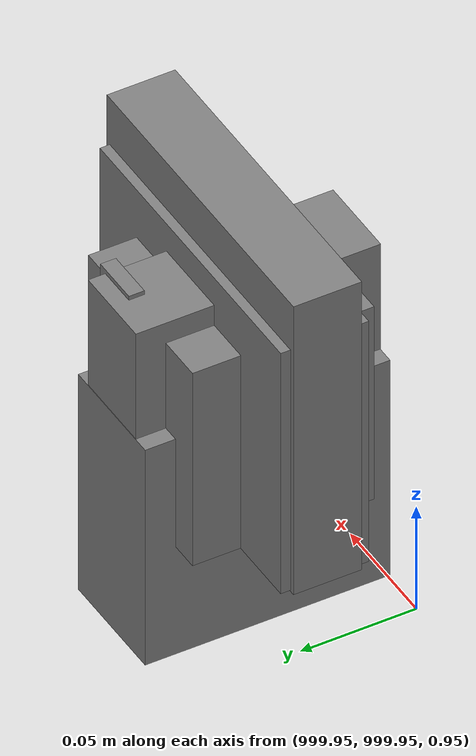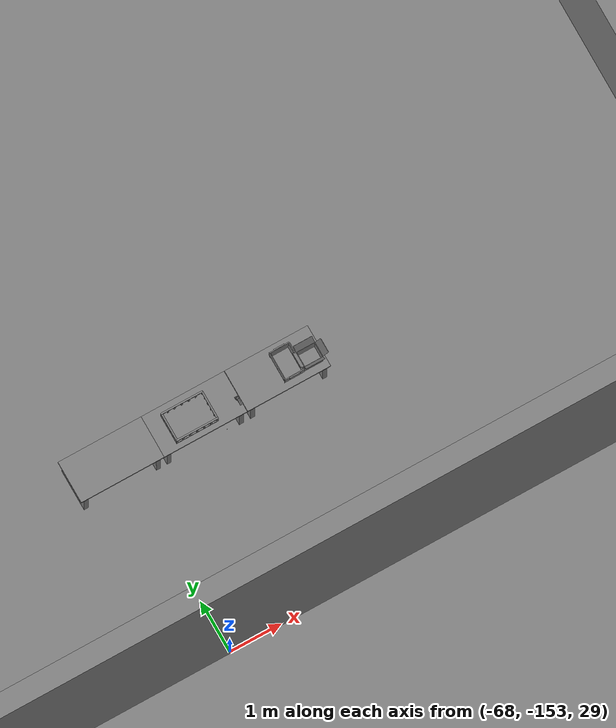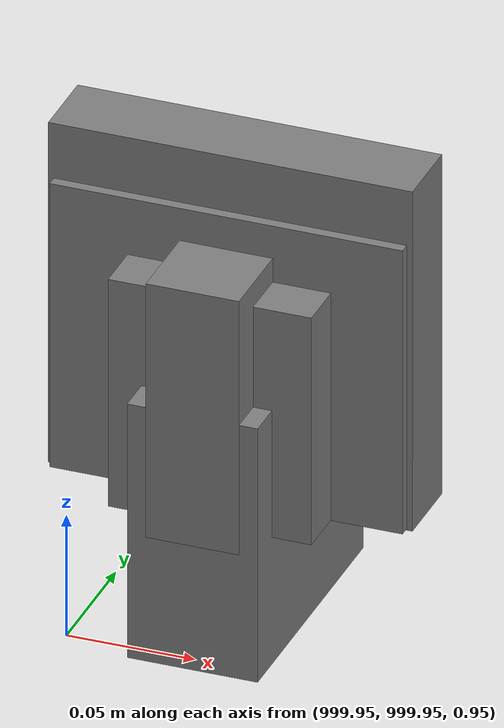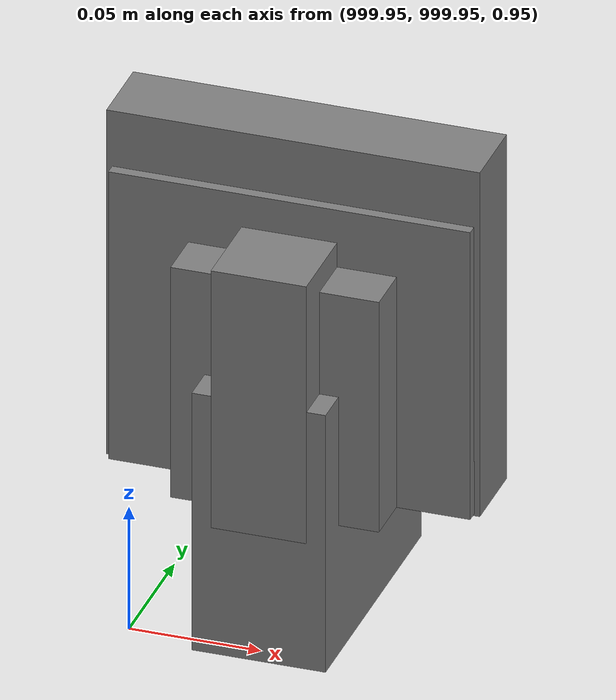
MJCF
<mujoco>
    <option gravity="0.000000000 0.000000000 -9.810000420" timestep="0.0049999999" integrator="implicitfast" density="1.225" viscosity="1.8000001e-05" noslip_iterations="10" iterations="100" sdf_iterations="50">
        <flag multiccd="disable"/>
    </option>
    <size memory="1000M"/>
    <compiler coordinate="local"/>
    <worldbody>
        <light cutoff="30" pos="0 1 1" dir="0 -1 -2"/>
        <light cutoff="30" pos="0 -1 1" dir="0 1 -2"/>
        <body pos="-65.890403748 -149.646896362 31.169471741" euler="81.326728821 56.421222687 -92.826255798" mocap="true" name="spotlight4_SpotLight"/>
        <body pos="1000.000000000 1000.000000000 1.000000000" euler="0.000000000 0.000000000 180.000000000" name="openloong_gripper_2f85_fix_base_usda_battery_01">
            <geom contype="1" conaffinity="1" density="1000" type="box" material="" rgba="0.500000000 0.500000000 0.500000000 1.000000000" solimp="0.899999976 0.949999988 0.001000000" friction="1.000000000 0.005000000 0.000100000" solref="0.020000000 1.000000000" margin="0" condim="3" group="0" pos="-0.011123657 -0.041940309 0.101691343" quat="1.000000000 0.000000000 0.000000000 0.000000000" size="0.010800000 0.003375000 0.004725000" name="openloong_gripper_2f85_fix_base_usda_geom_53C62E36_9A47_4C41_A17F_0102D85DCA47"/>
            <geom contype="1" conaffinity="1" density="1000" type="box" material="" rgba="0.500000000 0.500000000 0.500000000 1.000000000" solimp="0.899999976 0.949999988 0.001000000" friction="1.000000000 0.005000000 0.000100000" solref="0.020000000 1.000000000" margin="0" condim="3" group="0" pos="-0.010876465 -0.044247437 0.047066893" quat="0.998702705 -0.050920475 0.000000000 0.000000000" size="0.009450001 0.002700000 0.024975000" name="openloong_gripper_2f85_fix_base_usda_geom_353DCC20_466C_4E5A_AD87_E37A65AD3F15"/>
            <geom contype="1" conaffinity="1" density="1000" type="box" material="" rgba="0.500000000 0.500000000 0.500000000 1.000000000" solimp="0.899999976 0.949999988 0.001000000" friction="1.000000000 0.005000000 0.000100000" solref="0.020000000 1.000000000" margin="0" condim="3" group="0" pos="-0.001235962 -0.000659180 0.047381196" quat="1.000000000 0.000000000 0.000000000 0.000000000" size="0.039420001 0.039150000 0.047250003" name="openloong_gripper_2f85_fix_base_usda_geom_3F935604_44B0_45E6_926A_09D961BFF5C7"/>
            <geom contype="1" conaffinity="1" density="1000" type="box" material="" rgba="0.500000000 0.500000000 0.500000000 1.000000000" solimp="0.899999976 0.949999988 0.001000000" friction="1.000000000 0.005000000 0.000100000" solref="0.020000000 1.000000000" margin="0" condim="3" group="0" pos="-0.010876465 -0.039138794 0.009851727" quat="1.000000000 0.000000000 0.000000000 0.000000000" size="0.009450001 0.010800000 0.013500000" name="openloong_gripper_2f85_fix_base_usda_geom_58C37E3F_2077_4753_88E0_C9CF8150CA9E"/>
            <geom contype="1" conaffinity="1" density="1000" type="box" material="" rgba="0.500000000 0.500000000 0.500000000 1.000000000" solimp="0.899999976 0.949999988 0.001000000" friction="1.000000000 0.005000000 0.000100000" solref="0.020000000 1.000000000" margin="0" condim="3" group="0" pos="-0.010876465 -0.041528322 0.071508206" quat="1.000000000 0.000000000 0.000000000 0.000000000" size="0.009450001 0.002700000 0.027000001" name="openloong_gripper_2f85_fix_base_usda_geom_7C0E9647_E39B_48B5_9B75_C60579580E55"/>
            <freejoint name="openloong_gripper_2f85_fix_base_usda_battery_01_joint"/>
            <site size="0.005000000 0.005000000 0.005000000" rgba="0.500000000 0.500000000 0.500000000 1.000000000" pos="0.000000000 0.000000000 0.000000000" quat="0.999961913 0.008726500 0.000000000 0.000000000" group="0" type="sphere" name="openloong_gripper_2f85_fix_base_usda_battery_01site"/>
        </body>
        <body pos="-65.866943359 -148.903961182 31.163974762" euler="170.172241211 -40.994384766 -11.543854713" mocap="true" name="spotlight3_SpotLight"/>
        <body pos="1000.000000000 1000.000000000 1.000000000" euler="0.000000000 0.000000000 180.000000000" name="openloong_gripper_2f85_fix_base_usda_cpu_fan">
            <geom contype="1" conaffinity="1" density="1000" type="box" material="" rgba="0.500000000 0.500000000 0.500000000 1.000000000" solimp="0.899999976 0.949999988 0.001000000" friction="1.000000000 0.005000000 0.000100000" solref="0.020000000 1.000000000" margin="0" condim="3" group="0" pos="0.000000000 0.000000000 0.070034981" quat="0.000000000 0.000000000 0.000000000 1.000000000" size="0.070700005 0.014699999 0.070700005" name="openloong_gripper_2f85_fix_base_usda_geom_5D7ACD60_387B_4D3A_B7CA_C48265983ECB"/>
            <freejoint name="openloong_gripper_2f85_fix_base_usda_cpu_fan_joint"/>
            <site size="0.005000000 0.005000000 0.005000000" rgba="0.500000000 0.500000000 0.500000000 1.000000000" pos="0.000000000 0.000000000 0.000000000" quat="0.999961913 0.008726535 0.000000000 0.000000000" group="0" type="sphere" name="openloong_gripper_2f85_fix_base_usda_cpu_fancsite"/>
        </body>
        <body pos="1000.000000000 1000.000000000 1.000000000" euler="0.000000000 0.000000000 180.000000000" name="openloong_gripper_2f85_fix_base_usda_wifi_box">
            <geom contype="1" conaffinity="1" density="1000" type="box" material="" rgba="0.500000000 0.500000000 0.500000000 1.000000000" solimp="0.899999976 0.949999988 0.001000000" friction="1.000000000 0.005000000 0.000100000" solref="0.020000000 1.000000000" margin="0" condim="3" group="0" pos="0.000000000 0.000000000 0.058978677" quat="0.000000000 0.000000047 0.000000000 1.000000000" size="0.068499997 0.018999999 0.059000000" name="openloong_gripper_2f85_fix_base_usda_geom_55288D76_219E_4C72_A61C_4CB9AE187A82"/>
            <freejoint name="openloong_gripper_2f85_fix_base_usda_wifi_box_joint"/>
            <site size="0.005000000 0.005000000 0.005000000" rgba="0.500000000 0.500000000 0.500000000 1.000000000" pos="0.000000000 0.000000000 0.000000000" quat="0.999961913 0.008726500 0.000000000 0.000000000" group="0" type="sphere" name="openloong_gripper_2f85_fix_base_usda_wifi_boxsite"/>
        </body>
        <body pos="1000.000000000 1000.000000000 1.000000000" euler="0.000011953 0.000005123 -179.999984741" name="openloong_gripper_2f85_fix_base_usda_intel_box">
            <geom contype="1" conaffinity="1" density="1000" type="box" material="" rgba="0.500000000 0.500000000 0.500000000 1.000000000" solimp="0.899999976 0.949999988 0.001000000" friction="1.000000000 0.005000000 0.000100000" solref="0.020000000 1.000000000" margin="0" condim="3" group="0" pos="0.000000000 -0.000067139 0.000082284" quat="0.707106709 0.000000225 0.000000253 0.707106650" size="0.052800003 0.025300000 0.052800003" name="openloong_gripper_2f85_fix_base_usda_geom_549F2B20_19A5_4631_9B72_80CD4BB5FB6E"/>
            <freejoint name="openloong_gripper_2f85_fix_base_usda_intel_box_joint"/>
            <site size="0.005000000 0.005000000 0.005000000" rgba="0.500000000 0.500000000 0.500000000 1.000000000" pos="0.000000000 0.000000000 0.000000000" quat="0.999961913 0.008726500 0.000000000 0.000000000" group="0" type="sphere" name="openloong_gripper_2f85_fix_base_usda_intel_boxsite"/>
        </body>
        <body pos="1000.000000000 999.999938965 1.000000000" euler="0.000000000 0.000000000 180.000000000" name="openloong_gripper_2f85_fix_base_usda_intelcore_i5">
            <geom contype="1" conaffinity="1" density="1000" type="box" material="" rgba="0.500000000 0.500000000 0.500000000 1.000000000" solimp="0.899999976 0.949999988 0.001000000" friction="1.000000000 0.005000000 0.000100000" solref="0.020000000 1.000000000" margin="0" condim="3" group="0" pos="0.000000000 0.000000000 0.051722717" quat="0.707106709 0.000000000 0.000000000 -0.707106769" size="0.052800000 0.018080002 0.052800000" name="openloong_gripper_2f85_fix_base_usda_geom_F322ADE1_3F60_411E_8D56_EABA382306F7"/>
            <freejoint name="openloong_gripper_2f85_fix_base_usda_intelcore_i5_joint"/>
            <site size="0.005000000 0.005000000 0.005000000" rgba="0.500000000 0.500000000 0.500000000 1.000000000" pos="0.000000000 0.000000000 0.000000000" quat="0.999961913 0.008726534 0.000000000 0.000000000" group="0" type="sphere" name="openloong_gripper_2f85_fix_base_usda_intelcore_i5site"/>
        </body>
        <body pos="-65.815307617 -149.668045044 31.170461655" euler="-32.587371826 64.049034119 40.637573242" mocap="true" name="spotlight1_SpotLight"/>
        <body pos="-64.866622925 -149.383972168 30.183746338" euler="89.999984741 89.999946594 0.000000000" name="openloong_gripper_2f85_fix_base_usda_bluebox_01">
            <geom contype="1" conaffinity="1" density="1000" type="box" material="" rgba="0.500000000 0.500000000 0.500000000 1.000000000" solimp="0.899999976 0.949999988 0.001000000" friction="1.000000000 0.005000000 0.000100000" solref="0.020000000 1.000000000" margin="0" condim="3" group="0" pos="0.276580811 0.187225342 0.000068665" quat="0.707106948 0.000077471 0.707106352 0.000077486" size="0.100000001 0.057999998 0.010000000" name="openloong_gripper_2f85_fix_base_usda_geom_2B2B4D48_DE98_4204_B053_26629E14E5B7"/>
            <geom contype="1" conaffinity="1" density="1000" type="box" material="" rgba="0.500000000 0.500000000 0.500000000 1.000000000" solimp="0.899999976 0.949999988 0.001000000" friction="1.000000000 0.005000000 0.000100000" solref="0.020000000 1.000000000" margin="0" condim="3" group="0" pos="0.000000000 0.002883911 0.000000000" quat="0.999999881 0.000000000 0.000000000 0.000000000" size="0.254000008 0.003000000 0.172000006" name="openloong_gripper_2f85_fix_base_usda_geom_A8ED1AEB_2E2F_4203_9817_457CA5002C1B"/>
            <geom contype="1" conaffinity="1" density="1000" type="box" material="" rgba="0.500000000 0.500000000 0.500000000 1.000000000" solimp="0.899999976 0.949999988 0.001000000" friction="1.000000000 0.005000000 0.000100000" solref="0.020000000 1.000000000" margin="0" condim="3" group="0" pos="0.000000000 0.124874115 0.173484802" quat="0.999796331 0.020176515 -0.000000015 0.000000030" size="0.259999990 0.119999997 0.007000000" name="openloong_gripper_2f85_fix_base_usda_geom_17E6F802_CE67_4544_A830_9DAFDE2959C0"/>
            <geom contype="1" conaffinity="1" density="1000" type="box" material="" rgba="0.500000000 0.500000000 0.500000000 1.000000000" solimp="0.899999976 0.949999988 0.001000000" friction="1.000000000 0.005000000 0.000100000" solref="0.020000000 1.000000000" margin="0" condim="3" group="0" pos="0.000000000 0.124874115 -0.173469543" quat="0.999796331 -0.020176545 -0.000000015 0.000000000" size="0.259999990 0.119999997 0.007000000" name="openloong_gripper_2f85_fix_base_usda_geom_98A8E4E5_1231_4B38_910F_DF5E8108FDC7"/>
            <geom contype="1" conaffinity="1" density="1000" type="box" material="" rgba="0.500000000 0.500000000 0.500000000 1.000000000" solimp="0.899999976 0.949999988 0.001000000" friction="1.000000000 0.005000000 0.000100000" solref="0.020000000 1.000000000" margin="0" condim="3" group="0" pos="0.000000000 0.214008331 0.188980103" quat="0.999912977 0.013176724 0.000000015 0.000000000" size="0.259999990 0.029999999 0.012500000" name="openloong_gripper_2f85_fix_base_usda_geom_89CE80C5_88C3_4E03_9789_49AC2F1C9130"/>
            <geom contype="1" conaffinity="1" density="1000" type="box" material="" rgba="0.500000000 0.500000000 0.500000000 1.000000000" solimp="0.899999976 0.949999988 0.001000000" friction="1.000000000 0.005000000 0.000100000" solref="0.020000000 1.000000000" margin="0" condim="3" group="0" pos="-0.258361816 0.125289917 0.001876831" quat="0.702796936 -0.020792112 0.710783124 0.020769298" size="0.189999998 0.119999997 0.009000000" name="openloong_gripper_2f85_fix_base_usda_geom_59E268B5_13AA_4D0B_85C7_FFF728DA9B63"/>
            <geom contype="1" conaffinity="1" density="1000" type="box" material="" rgba="0.500000000 0.500000000 0.500000000 1.000000000" solimp="0.899999976 0.949999988 0.001000000" friction="1.000000000 0.005000000 0.000100000" solref="0.020000000 1.000000000" margin="0" condim="3" group="0" pos="0.000000000 0.214008331 -0.188980103" quat="0.999912977 -0.013176769 0.000000030 0.000000015" size="0.259999990 0.029999999 0.012500000" name="openloong_gripper_2f85_fix_base_usda_geom_72240768_5C26_4D1B_BA75_627E5629329A"/>
            <geom contype="1" conaffinity="1" density="1000" type="box" material="" rgba="0.500000000 0.500000000 0.500000000 1.000000000" solimp="0.899999976 0.949999988 0.001000000" friction="1.000000000 0.005000000 0.000100000" solref="0.020000000 1.000000000" margin="0" condim="3" group="0" pos="-0.276611328 0.187225342 0.000068665" quat="0.707106650 0.000077441 0.707106709 0.000077456" size="0.100000001 0.057999998 0.010000000" name="openloong_gripper_2f85_fix_base_usda_geom_C2644E97_2B5E_42EC_92EE_5CBEEBE04BB8"/>
            <geom contype="1" conaffinity="1" density="1000" type="box" material="" rgba="0.500000000 0.500000000 0.500000000 1.000000000" solimp="0.899999976 0.949999988 0.001000000" friction="1.000000000 0.005000000 0.000100000" solref="0.020000000 1.000000000" margin="0" condim="3" group="0" pos="0.258331299 0.125289917 0.001876831" quat="0.702851415 0.018856421 0.710823774 -0.019329369" size="0.189999998 0.119999997 0.009000000" name="openloong_gripper_2f85_fix_base_usda_geom_10A28A4A_12E5_4C21_92D2_ACC5C8A8AA1E"/>
            <freejoint name="openloong_gripper_2f85_fix_base_usda_bluebox_01_joint"/>
            <site size="0.005000000 0.005000000 0.005000000" rgba="0.500000000 0.500000000 0.500000000 1.000000000" pos="0.000000000 0.000000000 0.000000000" quat="0.999961913 0.008726534 0.000000000 0.000000000" group="0" type="sphere" name="openloong_gripper_2f85_fix_base_usda_bluebox_01site"/>
        </body>
        <body pos="-64.496299744 -149.491867065 30.235729218" euler="0.000000000 0.000000000 89.999946594" name="openloong_gripper_2f85_fix_base_usda_cardboardbox_01">
            <geom contype="1" conaffinity="1" density="1000" type="box" material="" rgba="0.500000000 0.500000000 0.500000000 1.000000000" solimp="0.899999976 0.949999988 0.001000000" friction="1.000000000 0.005000000 0.000100000" solref="0.020000000 1.000000000" margin="0" condim="3" group="0" pos="-0.003166199 -0.004086494 0.005052090" quat="1.000000000 0.000000000 0.000000000 0.000000000" size="0.142499998 0.177500010 0.005000000" name="openloong_gripper_2f85_fix_base_usda_geom_CFBD942E_5A60_4F95_A0E1_B002D5A14967"/>
            <geom contype="1" conaffinity="1" density="1000" type="box" material="" rgba="0.500000000 0.500000000 0.500000000 1.000000000" solimp="0.899999976 0.949999988 0.001000000" friction="1.000000000 0.005000000 0.000100000" solref="0.020000000 1.000000000" margin="0" condim="3" group="0" pos="-0.003166199 0.170316696 0.150570869" quat="1.000000000 0.000000000 0.000000000 0.000000000" size="0.142499998 0.005000000 0.149999991" name="openloong_gripper_2f85_fix_base_usda_geom_C97A5B28_071A_41D0_A5C1_888DE54C23C1"/>
            <geom contype="1" conaffinity="1" density="1000" type="box" material="" rgba="0.500000000 0.500000000 0.500000000 1.000000000" solimp="0.899999976 0.949999988 0.001000000" friction="1.000000000 0.005000000 0.000100000" solref="0.020000000 1.000000000" margin="0" condim="3" group="0" pos="-0.147399902 -0.005307198 0.150570869" quat="1.000000000 0.000000000 0.000000000 0.000000000" size="0.005000000 0.177500010 0.149999991" name="openloong_gripper_2f85_fix_base_usda_geom_CBF585F2_F35B_4586_88DB_4123BD65C264"/>
            <geom contype="1" conaffinity="1" density="1000" type="box" material="" rgba="0.500000000 0.500000000 0.500000000 1.000000000" solimp="0.899999976 0.949999988 0.001000000" friction="1.000000000 0.005000000 0.000100000" solref="0.020000000 1.000000000" margin="0" condim="3" group="0" pos="0.140275955 -0.005307198 0.150570869" quat="1.000000000 0.000000000 0.000000000 0.000000000" size="0.005000000 0.177500010 0.149999991" name="openloong_gripper_2f85_fix_base_usda_geom_CC1090DD_9015_4C22_A728_B82002567F5D"/>
            <geom contype="1" conaffinity="1" density="1000" type="box" material="" rgba="0.500000000 0.500000000 0.500000000 1.000000000" solimp="0.899999976 0.949999988 0.001000000" friction="1.000000000 0.005000000 0.000100000" solref="0.020000000 1.000000000" margin="0" condim="3" group="0" pos="-0.003166199 -0.181550980 0.150570869" quat="1.000000000 0.000000000 0.000000000 0.000000000" size="0.142499998 0.005000000 0.149999991" name="openloong_gripper_2f85_fix_base_usda_geom_1E7173AD_F4C2_4262_B68D_DB65748DC519"/>
            <freejoint name="openloong_gripper_2f85_fix_base_usda_cardboardbox_01_joint"/>
            <site size="0.005000000 0.005000000 0.005000000" rgba="0.500000000 0.500000000 0.500000000 1.000000000" pos="0.000000000 0.000000000 0.000000000" quat="0.999961913 0.008726535 0.000000000 0.000000000" group="0" type="sphere" name="openloong_gripper_2f85_fix_base_usda_site_E2E56BC7_627C_4848_95D1_7B03C996C21C"/>
            <body pos="0.139160156 -0.004048347 0.301930904" euler="-179.999954224 49.383502960 179.999954224" name="openloong_gripper_2f85_fix_base_usda_A1_006">
                <geom contype="1" conaffinity="1" density="1000" type="box" material="" rgba="0.500000000 0.500000000 0.500000000 1.000000000" solimp="0.899999976 0.949999988 0.001000000" friction="1.000000000 0.005000000 0.000100000" solref="0.020000000 1.000000000" margin="0" condim="3" group="0" pos="-0.071587563 0.000009537 0.001745224" quat="0.999999881 0.000000000 0.000000000 0.000000000" size="0.071249999 0.179999992 0.002500000" name="openloong_gripper_2f85_fix_base_usda_geom_42948F37_16BC_41CD_8424_0CC63744D020"/>
                <joint armature="0" stiffness="0.07" damping="0.0099999998" axis="0.000000 1.000000 0.000000" type="hinge" name="openloong_gripper_2f85_fix_base_usda_A1_006"/>
            </body>
            <body pos="-0.145902634 -0.004086494 0.301938057" euler="-180.000000000 -60.000011444 -180.000000000" name="openloong_gripper_2f85_fix_base_usda_A2_006">
                <geom contype="1" conaffinity="1" density="1000" type="box" material="" rgba="0.500000000 0.500000000 0.500000000 1.000000000" solimp="0.899999976 0.949999988 0.001000000" friction="1.000000000 0.005000000 0.000100000" solref="0.020000000 1.000000000" margin="0" condim="3" group="0" pos="0.071268082 0.000009537 0.002717972" quat="0.000002921 0.000000000 -0.000000030 0.999999881" size="0.071249999 0.179999992 0.002500000" name="openloong_gripper_2f85_fix_base_usda_geom_C6DAC66C_3ECB_43BF_A783_48055F6F9FF3"/>
                <joint armature="0" stiffness="0.07" damping="0.0099999998" axis="0.000000 1.000000 0.000000" type="hinge" name="openloong_gripper_2f85_fix_base_usda_A2_006"/>
            </body>
            <body pos="-0.003385544 0.175991058 0.301930904" euler="-125.858116150 -0.000004561 0.000002331" name="openloong_gripper_2f85_fix_base_usda_B2_006">
                <geom contype="1" conaffinity="1" density="1000" type="box" material="" rgba="0.500000000 0.500000000 0.500000000 1.000000000" solimp="0.899999976 0.949999988 0.001000000" friction="1.000000000 0.005000000 0.000100000" solref="0.020000000 1.000000000" margin="0" condim="3" group="0" pos="0.000009537 -0.070939064 -0.002470016" quat="0.999614120 0.027776197 -0.000000015 0.000000030" size="0.137500003 0.064999998 0.005000000" name="openloong_gripper_2f85_fix_base_usda_geom_78E3ECE2_E3F0_45E2_9974_FFBD6724FEB2"/>
                <joint armature="0" stiffness="0.07" damping="0.0099999998" axis="1.000000 0.000000 0.000000" type="hinge" name="openloong_gripper_2f85_fix_base_usda_B2_006"/>
            </body>
            <body pos="-0.003385544 -0.184140205 0.301938057" euler="147.805557251 0.000000000 0.000000000" name="openloong_gripper_2f85_fix_base_usda_B1_006">
                <geom contype="1" conaffinity="1" density="1000" type="box" material="" rgba="0.500000000 0.500000000 0.500000000 1.000000000" solimp="0.899999976 0.949999988 0.001000000" friction="1.000000000 0.005000000 0.000100000" solref="0.020000000 1.000000000" margin="0" condim="3" group="0" pos="-0.000028610 0.070202351 -0.002703667" quat="0.999614179 -0.027776167 0.000000000 0.000000000" size="0.137500003 0.064999998 0.005000000" name="openloong_gripper_2f85_fix_base_usda_geom_FF985041_DA35_4782_8690_830D7F989BA8"/>
                <joint armature="0" stiffness="0.07" damping="0.0099999998" axis="1.000000 0.000000 0.000000" type="hinge" name="openloong_gripper_2f85_fix_base_usda_B1_006"/>
            </body>
        </body>
        <body pos="-65.882858276 -149.481979370 30.229999542" euler="-64.487716675 0.000000000 0.000000000" name="openloong_gripper_2f85_fix_base_usda_Barcode">
            <geom contype="1" conaffinity="1" density="1000" type="box" material="" rgba="0.500000000 0.500000000 0.500000000 1.000000000" solimp="0.899999976 0.949999988 0.001000000" friction="1.000000000 0.005000000 0.000100000" solref="0.020000000 1.000000000" margin="0" condim="3" group="0" pos="0.000000000 0.013038635 0.001419067" quat="0.000000000 0.000000000 0.000000000 1.000000119" size="0.034000002 0.010000000 0.017999999" name="openloong_gripper_2f85_fix_base_usda_geom_B6D15B74_5180_4DDE_B3B5_82FB5C53D111"/>
            <geom contype="1" conaffinity="1" density="1000" type="box" material="" rgba="0.500000000 0.500000000 0.500000000 1.000000000" solimp="0.899999976 0.949999988 0.001000000" friction="1.000000000 0.005000000 0.000100000" solref="0.020000000 1.000000000" margin="0" condim="3" group="0" pos="0.000000000 -0.035301208 -0.007095337" quat="0.000000000 0.000000000 -0.043619365 0.999048233" size="0.028999999 0.010000000 0.020000000" name="openloong_gripper_2f85_fix_base_usda_geom_DA0D9343_845F_44A3_A86E_B8EFA0FFE5EA"/>
            <geom contype="1" conaffinity="1" density="1000" type="box" material="" rgba="0.500000000 0.500000000 0.500000000 1.000000000" solimp="0.899999976 0.949999988 0.001000000" friction="1.000000000 0.005000000 0.000100000" solref="0.020000000 1.000000000" margin="0" condim="3" group="0" pos="0.000000000 -0.043411255 -0.011749268" quat="0.922262907 0.386563420 0.000000000 0.000000000" size="0.026000001 0.010000000 0.020000000" name="openloong_gripper_2f85_fix_base_usda_geom_2F6F3069_627D_4018_AA07_3CDA62BB484E"/>
            <geom contype="1" conaffinity="1" density="1000" type="box" material="" rgba="0.500000000 0.500000000 0.500000000 1.000000000" solimp="0.899999976 0.949999988 0.001000000" friction="1.000000000 0.005000000 0.000100000" solref="0.020000000 1.000000000" margin="0" condim="3" group="0" pos="0.000000000 -0.016967773 -0.031860352" quat="0.000000000 0.000000000 0.000000000 1.000000119" size="0.008000000 0.010000000 0.013000000" name="openloong_gripper_2f85_fix_base_usda_geom_57E0A617_B9B6_44CA_943D_59C4FC3226E1"/>
            <geom contype="1" conaffinity="1" density="1000" type="box" material="" rgba="0.500000000 0.500000000 0.500000000 1.000000000" solimp="0.899999976 0.949999988 0.001000000" friction="1.000000000 0.005000000 0.000100000" solref="0.020000000 1.000000000" margin="0" condim="3" group="0" pos="0.000000000 -0.001869202 0.000312805" quat="0.953716993 0.300705761 0.000000000 0.000000000" size="0.032000002 0.010000000 0.018999999" name="openloong_gripper_2f85_fix_base_usda_geom_61451B06_81E3_42BF_88DC_3331AB198F3E"/>
            <geom contype="1" conaffinity="1" density="1000" type="box" material="" rgba="0.500000000 0.500000000 0.500000000 1.000000000" solimp="0.899999976 0.949999988 0.001000000" friction="1.000000000 0.005000000 0.000100000" solref="0.020000000 1.000000000" margin="0" condim="3" group="0" pos="0.000000000 -0.019531250 -0.003173828" quat="0.953716993 0.300705761 0.000000000 0.000000000" size="0.030999999 0.010000000 0.020000000" name="openloong_gripper_2f85_fix_base_usda_geom_4B0661A1_4F8E_4A5D_A298_C5EE6F1D62A5"/>
            <geom contype="1" conaffinity="1" density="1000" type="box" material="" rgba="0.500000000 0.500000000 0.500000000 1.000000000" solimp="0.899999976 0.949999988 0.001000000" friction="1.000000000 0.005000000 0.000100000" solref="0.020000000 1.000000000" margin="0" condim="3" group="0" pos="0.000000000 -0.035301208 -0.007095337" quat="0.953716993 0.300705761 0.000000000 0.000000000" size="0.028999999 0.010000000 0.020000000" name="openloong_gripper_2f85_fix_base_usda_geom_E0C14E66_5105_4352_B1E9_80DB46D4FBF2"/>
            <geom contype="1" conaffinity="1" density="1000" type="box" material="" rgba="0.500000000 0.500000000 0.500000000 1.000000000" solimp="0.899999976 0.949999988 0.001000000" friction="1.000000000 0.005000000 0.000100000" solref="0.020000000 1.000000000" margin="0" condim="3" group="0" pos="0.000000000 -0.042617798 -0.071121216" quat="0.000000000 0.000000000 0.000000000 1.000000119" size="0.013000000 0.021000000 0.059999999" name="openloong_gripper_2f85_fix_base_usda_geom_2DE64694_8FEA_4F12_B3E9_CD787098D60C"/>
            <freejoint name="openloong_gripper_2f85_fix_base_usda_Barcode_joint"/>
            <site size="0.005000000 0.005000000 0.005000000" rgba="0.500000000 0.500000000 0.500000000 1.000000000" pos="0.000000000 0.000000000 0.000000000" quat="1.000000000 0.000000000 0.000000000 0.000000000" group="0" type="sphere" name="openloong_gripper_2f85_fix_base_usda_Barcode_site"/>
        </body>
        <body pos="-66.745018005 -149.392349243 30.184000015" euler="0.000000000 0.000000000 89.999946594" name="[22330408273082]_Basket_01">
            <geom contype="1" conaffinity="1" density="1000" type="box" material="" rgba="0.500000000 0.500000000 0.500000000 1.000000000" solimp="0.899999976 0.949999988 0.001000000" friction="1.000000000 0.005000000 0.000100000" solref="0.020000000 1.000000000" margin="0" condim="3" group="0" pos="-0.052425385 0.389207840 0.089787483" quat="0.707107008 0.000000000 0.000000000 0.707106411" size="0.014249999 0.014249999 0.059999999" name="[22330408273082]_geom_9EBAD601_1282_4CE8_A110_CB1B5B74162A"/>
            <geom contype="1" conaffinity="1" density="1000" type="box" material="" rgba="0.500000000 0.500000000 0.500000000 1.000000000" solimp="0.899999976 0.949999988 0.001000000" friction="1.000000000 0.005000000 0.000100000" solref="0.020000000 1.000000000" margin="0" condim="3" group="0" pos="0.264015198 -0.133043289 0.089787483" quat="0.707107008 0.000000000 0.000000000 0.707106411" size="0.014249999 0.014249999 0.059999999" name="[22330408273082]_geom_2281891B_8007_47F8_9BBA_1CCA40F08E3D"/>
            <geom contype="1" conaffinity="1" density="1000" type="box" material="" rgba="0.500000000 0.500000000 0.500000000 1.000000000" solimp="0.899999976 0.949999988 0.001000000" friction="1.000000000 0.005000000 0.000100000" solref="0.020000000 1.000000000" margin="0" condim="3" group="0" pos="-0.264015198 -0.265548706 0.089793205" quat="0.707107008 0.000000000 0.000000000 0.707106411" size="0.014249999 0.014249999 0.059999999" name="[22330408273082]_geom_C72C730C_409A_40D1_BFDE_996E4173F769"/>
            <geom contype="1" conaffinity="1" density="1000" type="box" material="" rgba="0.500000000 0.500000000 0.500000000 1.000000000" solimp="0.899999976 0.949999988 0.001000000" friction="1.000000000 0.005000000 0.000100000" solref="0.020000000 1.000000000" margin="0" condim="3" group="0" pos="-0.160263062 -0.389322281 0.089793205" quat="0.707107008 0.000000000 0.000000000 0.707106411" size="0.014249999 0.014249999 0.059999999" name="[22330408273082]_geom_AB97C4FE_041E_4CC0_9472_D538DF8561A0"/>
            <geom contype="1" conaffinity="1" density="1000" type="box" material="" rgba="0.500000000 0.500000000 0.500000000 1.000000000" solimp="0.899999976 0.949999988 0.001000000" friction="1.000000000 0.005000000 0.000100000" solref="0.020000000 1.000000000" margin="0" condim="3" group="0" pos="0.162265778 -0.389322281 0.089787483" quat="0.707107008 0.000000000 0.000000000 0.707106411" size="0.014249999 0.014249999 0.059999999" name="[22330408273082]_geom_92D315EF_543F_4427_B20D_AC77557DEF2D"/>
            <geom contype="1" conaffinity="1" density="1000" type="box" material="" rgba="0.500000000 0.500000000 0.500000000 1.000000000" solimp="0.899999976 0.949999988 0.001000000" friction="1.000000000 0.005000000 0.000100000" solref="0.020000000 1.000000000" margin="0" condim="3" group="0" pos="0.264015198 0.389207840 0.089787483" quat="0.707107008 0.000000000 0.000000000 0.707106411" size="0.014249999 0.014249999 0.059999999" name="[22330408273082]_geom_47BD4CC4_9CA0_4449_8EF0_428CA2E36AC5"/>
            <geom contype="1" conaffinity="1" density="1000" type="box" material="" rgba="0.500000000 0.500000000 0.500000000 1.000000000" solimp="0.899999976 0.949999988 0.001000000" friction="1.000000000 0.005000000 0.000100000" solref="0.020000000 1.000000000" margin="0" condim="3" group="0" pos="-0.264015198 -0.133043289 0.089793205" quat="0.707107008 0.000000000 0.000000000 0.707106411" size="0.014249999 0.014249999 0.059999999" name="[22330408273082]_geom_2D9599A1_0E7D_4672_A04A_6F7D5EE69B2C"/>
            <geom contype="1" conaffinity="1" density="1000" type="box" material="" rgba="0.500000000 0.500000000 0.500000000 1.000000000" solimp="0.899999976 0.949999988 0.001000000" friction="1.000000000 0.005000000 0.000100000" solref="0.020000000 1.000000000" margin="0" condim="3" group="0" pos="-0.264026642 0.269256592 0.089793205" quat="0.707107008 0.000000000 0.000000000 0.707106411" size="0.014249999 0.014249999 0.059999999" name="[22330408273082]_geom_9A60B9EF_C9D3_4833_937E_2D8AD1D02F46"/>
            <geom contype="1" conaffinity="1" density="1000" type="box" material="" rgba="0.500000000 0.500000000 0.500000000 1.000000000" solimp="0.899999976 0.949999988 0.001000000" friction="1.000000000 0.005000000 0.000100000" solref="0.020000000 1.000000000" margin="0" condim="3" group="0" pos="0.054462433 0.389207840 0.089787483" quat="0.707107008 0.000000000 0.000000000 0.707106411" size="0.014249999 0.014249999 0.059999999" name="[22330408273082]_geom_C2ACD11F_E148_4079_BC5E_25044C3151BE"/>
            <geom contype="1" conaffinity="1" density="1000" type="box" material="" rgba="0.500000000 0.500000000 0.500000000 1.000000000" solimp="0.899999976 0.949999988 0.001000000" friction="1.000000000 0.005000000 0.000100000" solref="0.020000000 1.000000000" margin="0" condim="3" group="0" pos="0.054462433 -0.389322281 0.089787483" quat="0.707107008 0.000000000 0.000000000 0.707106411" size="0.014249999 0.014249999 0.059999999" name="[22330408273082]_geom_6DA7250F_27A5_4DC9_A845_508B5EB678F8"/>
            <geom contype="1" conaffinity="1" density="1000" type="box" material="" rgba="0.500000000 0.500000000 0.500000000 1.000000000" solimp="0.899999976 0.949999988 0.001000000" friction="1.000000000 0.005000000 0.000100000" solref="0.020000000 1.000000000" margin="0" condim="3" group="0" pos="0.264015198 0.269256592 0.089793205" quat="0.707107008 0.000000000 0.000000000 0.707106411" size="0.014249999 0.014249999 0.059999999" name="[22330408273082]_geom_FE19836D_0D1D_46EA_BFC1_7D31784A52B8"/>
            <geom contype="1" conaffinity="1" density="1000" type="box" material="" rgba="0.500000000 0.500000000 0.500000000 1.000000000" solimp="0.899999976 0.949999988 0.001000000" friction="1.000000000 0.005000000 0.000100000" solref="0.020000000 1.000000000" margin="0" condim="3" group="0" pos="0.264015198 -0.389322281 0.089787483" quat="0.707107008 0.000000000 0.000000000 0.707106411" size="0.014249999 0.014249999 0.059999999" name="[22330408273082]_geom_3FC72A04_E2B8_4979_B5E9_1922EA22A0E4"/>
            <geom contype="1" conaffinity="1" density="1000" type="box" material="" rgba="0.500000000 0.500000000 0.500000000 1.000000000" solimp="0.899999976 0.949999988 0.001000000" friction="1.000000000 0.005000000 0.000100000" solref="0.020000000 1.000000000" margin="0" condim="3" group="0" pos="0.000000000 0.000000000 0.015998840" quat="0.707107008 0.000000000 0.000000000 0.707106411" size="0.403499991 0.279000014 0.015750000" name="[22330408273082]_geom_BB6676D0_3E03_4C0E_ACB1_7857D90991E4"/>
            <geom contype="1" conaffinity="1" density="1000" type="box" material="" rgba="0.500000000 0.500000000 0.500000000 1.000000000" solimp="0.899999976 0.949999988 0.001000000" friction="1.000000000 0.005000000 0.000100000" solref="0.020000000 1.000000000" margin="0" condim="3" group="0" pos="0.000000000 -0.389476776 0.163619041" quat="0.707107008 0.000000000 0.000000000 0.707106411" size="0.015000000 0.277500004 0.015750000" name="[22330408273082]_geom_8B9BB095_F345_420F_BCB5_1F963E69DC82"/>
            <geom contype="1" conaffinity="1" density="1000" type="box" material="" rgba="0.500000000 0.500000000 0.500000000 1.000000000" solimp="0.899999976 0.949999988 0.001000000" friction="1.000000000 0.005000000 0.000100000" solref="0.020000000 1.000000000" margin="0" condim="3" group="0" pos="0.162265778 0.389207840 0.089787483" quat="0.707107008 0.000000000 0.000000000 0.707106411" size="0.014249999 0.014249999 0.059999999" name="[22330408273082]_geom_1C70A297_5831_43A5_8FFA_86FA38FFD1F4"/>
            <geom contype="1" conaffinity="1" density="1000" type="box" material="" rgba="0.500000000 0.500000000 0.500000000 1.000000000" solimp="0.899999976 0.949999988 0.001000000" friction="1.000000000 0.005000000 0.000100000" solref="0.020000000 1.000000000" margin="0" condim="3" group="0" pos="0.000000000 0.389471054 0.163619041" quat="0.707107008 0.000000000 0.000000000 0.707106411" size="0.015000000 0.277500004 0.015750000" name="[22330408273082]_geom_B23E74F7_BA2C_4FD2_B141_C4D4A514DBC2"/>
            <geom contype="1" conaffinity="1" density="1000" type="box" material="" rgba="0.500000000 0.500000000 0.500000000 1.000000000" solimp="0.899999976 0.949999988 0.001000000" friction="1.000000000 0.005000000 0.000100000" solref="0.020000000 1.000000000" margin="0" condim="3" group="0" pos="-0.263511658 0.000000000 0.163619041" quat="0.707107008 0.000000000 0.000000000 0.707106411" size="0.403499991 0.015000000 0.015750000" name="[22330408273082]_geom_407DBAE9_FB97_44D2_B9C4_A9F88CB24A28"/>
            <geom contype="1" conaffinity="1" density="1000" type="box" material="" rgba="0.500000000 0.500000000 0.500000000 1.000000000" solimp="0.899999976 0.949999988 0.001000000" friction="1.000000000 0.005000000 0.000100000" solref="0.020000000 1.000000000" margin="0" condim="3" group="0" pos="-0.264015198 0.141334534 0.089793205" quat="0.707107008 0.000000000 0.000000000 0.707106411" size="0.014249999 0.014249999 0.059999999" name="[22330408273082]_geom_AC8EAFDF_AF1B_4F03_83AE_A0C78E44E0E9"/>
            <geom contype="1" conaffinity="1" density="1000" type="box" material="" rgba="0.500000000 0.500000000 0.500000000 1.000000000" solimp="0.899999976 0.949999988 0.001000000" friction="1.000000000 0.005000000 0.000100000" solref="0.020000000 1.000000000" margin="0" condim="3" group="0" pos="0.264015198 -0.265548706 0.089787483" quat="0.707107008 0.000000000 0.000000000 0.707106411" size="0.014249999 0.014249999 0.059999999" name="[22330408273082]_geom_65B6403D_CAF1_4AB1_BBC2_AF1C74C7178D"/>
            <geom contype="1" conaffinity="1" density="1000" type="box" material="" rgba="0.500000000 0.500000000 0.500000000 1.000000000" solimp="0.899999976 0.949999988 0.001000000" friction="1.000000000 0.005000000 0.000100000" solref="0.020000000 1.000000000" margin="0" condim="3" group="0" pos="-0.160263062 0.389207840 0.089787483" quat="0.707107008 0.000000000 0.000000000 0.707106411" size="0.014249999 0.014249999 0.059999999" name="[22330408273082]_geom_1B53D307_D462_432D_9186_7D75177DF845"/>
            <geom contype="1" conaffinity="1" density="1000" type="box" material="" rgba="0.500000000 0.500000000 0.500000000 1.000000000" solimp="0.899999976 0.949999988 0.001000000" friction="1.000000000 0.005000000 0.000100000" solref="0.020000000 1.000000000" margin="0" condim="3" group="0" pos="-0.052425385 -0.389322281 0.089787483" quat="0.707107008 0.000000000 0.000000000 0.707106411" size="0.014249999 0.014249999 0.059999999" name="[22330408273082]_geom_A31C15D8_F8A2_44A0_8C00_FA8C296A1F80"/>
            <geom contype="1" conaffinity="1" density="1000" type="box" material="" rgba="0.500000000 0.500000000 0.500000000 1.000000000" solimp="0.899999976 0.949999988 0.001000000" friction="1.000000000 0.005000000 0.000100000" solref="0.020000000 1.000000000" margin="0" condim="3" group="0" pos="-0.264026642 -0.389322281 0.089793205" quat="0.707107008 0.000000000 0.000000000 0.707106411" size="0.014249999 0.014249999 0.059999999" name="[22330408273082]_geom_F6ED9A1B_37C0_49A8_B7C4_7BC34EEBE91D"/>
            <geom contype="1" conaffinity="1" density="1000" type="box" material="" rgba="0.500000000 0.500000000 0.500000000 1.000000000" solimp="0.899999976 0.949999988 0.001000000" friction="1.000000000 0.005000000 0.000100000" solref="0.020000000 1.000000000" margin="0" condim="3" group="0" pos="0.264015198 0.141334534 0.089787483" quat="0.707107008 0.000000000 0.000000000 0.707106411" size="0.014249999 0.014249999 0.059999999" name="[22330408273082]_geom_86833FF9_7278_4F07_BD6C_B643F4AE14C4"/>
            <geom contype="1" conaffinity="1" density="1000" type="box" material="" rgba="0.500000000 0.500000000 0.500000000 1.000000000" solimp="0.899999976 0.949999988 0.001000000" friction="1.000000000 0.005000000 0.000100000" solref="0.020000000 1.000000000" margin="0" condim="3" group="0" pos="-0.264015198 0.389207840 0.089793205" quat="0.707107008 0.000000000 0.000000000 0.707106411" size="0.014249999 0.014249999 0.059999999" name="[22330408273082]_geom_E997A186_BF61_43A3_AACA_FEF353D0B76F"/>
            <geom contype="1" conaffinity="1" density="1000" type="box" material="" rgba="0.500000000 0.500000000 0.500000000 1.000000000" solimp="0.899999976 0.949999988 0.001000000" friction="1.000000000 0.005000000 0.000100000" solref="0.020000000 1.000000000" margin="0" condim="3" group="0" pos="0.264015198 0.004480362 0.089787483" quat="0.707107008 0.000000000 0.000000000 0.707106411" size="0.014249999 0.014249999 0.059999999" name="[22330408273082]_geom_5B7A4D05_C629_4005_B69B_74D6849D028F"/>
            <geom contype="1" conaffinity="1" density="1000" type="box" material="" rgba="0.500000000 0.500000000 0.500000000 1.000000000" solimp="0.899999976 0.949999988 0.001000000" friction="1.000000000 0.005000000 0.000100000" solref="0.020000000 1.000000000" margin="0" condim="3" group="0" pos="0.263694763 -0.000011444 0.163619041" quat="0.707107008 0.000000000 0.000000000 0.707106411" size="0.403499991 0.015000000 0.015750000" name="[22330408273082]_geom_35E34D69_2FD8_47C5_BD27_2AD3BA3975C7"/>
            <geom contype="1" conaffinity="1" density="1000" type="box" material="" rgba="0.500000000 0.500000000 0.500000000 1.000000000" solimp="0.899999976 0.949999988 0.001000000" friction="1.000000000 0.005000000 0.000100000" solref="0.020000000 1.000000000" margin="0" condim="3" group="0" pos="-0.264015198 0.004480362 0.089793205" quat="0.707107008 0.000000000 0.000000000 0.707106411" size="0.014249999 0.014249999 0.059999999" name="[22330408273082]_geom_A75A61BB_94C7_47C1_8BFD_80CEE43ADB2D"/>
            <freejoint name="[22330408273082]_joint_1E9C0AF1_E80E_465B_BC71_D225A8356C7B"/>
        </body>
        <body pos="0.000000000 0.000000000 0.000000000" euler="0.000000000 0.000000000 0.000000000" name="Static Objects_Static Objects">
            <geom contype="1" conaffinity="1" density="1000" type="box" material="" rgba="0.500000000 0.500000000 0.500000000 1.000000000" solimp="0.899999976 0.949999988 0.001000000" friction="1.000000000 0.005000000 0.000100000" solref="0.020000000 1.000000000" margin="0" condim="3" group="0" pos="-67.544113159 -149.365814209 29.727830887" quat="0.500000417 0.499999970 0.499999553 0.499999970" size="0.381000012 0.319999993 0.041000001" name="Static Objects_geom_F7CE2392_F165_4B84_A5CE_6B0118A50C6B"/>
            <geom contype="1" conaffinity="1" density="1000" type="box" material="" rgba="0.500000000 0.500000000 0.500000000 1.000000000" solimp="0.899999976 0.949999988 0.001000000" friction="1.000000000 0.005000000 0.000100000" solref="0.020000000 1.000000000" margin="0" condim="3" group="0" pos="-68.239501953 -149.365814209 30.086868286" quat="0.500000417 0.499999970 0.499999553 0.499999970" size="0.370999992 0.039500002 0.745000005" name="Static Objects_geom_9A85F50F_F9FF_48A6_BBFF_7854E55AA49D"/>
            <geom contype="1" conaffinity="1" density="1000" type="box" material="" rgba="0.500000000 0.500000000 0.500000000 1.000000000" solimp="0.899999976 0.949999988 0.001000000" friction="1.000000000 0.005000000 0.000100000" solref="0.020000000 1.000000000" margin="0" condim="3" group="0" pos="-68.239501953 -149.365814209 30.147235870" quat="0.500000417 0.499999970 0.499999553 0.499999970" size="0.400000006 0.022000000 0.800000012" name="Static Objects_geom_1E8EDD61_BF78_4CD2_AE41_BE656C581EE8"/>
            <geom contype="1" conaffinity="1" density="1000" type="box" material="" rgba="0.500000000 0.500000000 0.500000000 1.000000000" solimp="0.899999976 0.949999988 0.001000000" friction="1.000000000 0.005000000 0.000100000" solref="0.020000000 1.000000000" margin="0" condim="3" group="0" pos="-68.934890747 -149.365814209 29.727830887" quat="0.500000417 0.499999970 0.499999553 0.499999970" size="0.381000012 0.319999993 0.041000001" name="Static Objects_geom_12063619_7433_4A5D_8B2C_A899C844673E"/>
            <geom contype="1" conaffinity="1" density="1000" type="box" material="" rgba="0.500000000 0.500000000 0.500000000 1.000000000" solimp="0.899999976 0.949999988 0.001000000" friction="1.000000000 0.005000000 0.000100000" solref="0.020000000 1.000000000" margin="0" condim="3" group="0" pos="-68.239501953 -149.365814209 29.561563492" quat="0.500000417 0.499999970 0.499999553 0.499999970" size="0.020000000 0.022000000 0.660000026" name="Static Objects_geom_067E8697_06F4_448D_B1E9_1F595F491E1B"/>
            <geom contype="1" conaffinity="1" density="1000" type="box" material="" rgba="0.500000000 0.500000000 0.500000000 1.000000000" solimp="0.899999976 0.949999988 0.001000000" friction="1.000000000 0.005000000 0.000100000" solref="0.020000000 1.000000000" margin="0" condim="3" group="0" pos="-65.945671082 -149.365814209 29.727830887" quat="0.500000417 0.499999970 0.499999553 0.499999970" size="0.381000012 0.319999993 0.041000001" name="Static Objects_geom_295CFD4C_0A0D_4B63_8B88_80E81A3EB47C"/>
            <geom contype="1" conaffinity="1" density="1000" type="box" material="" rgba="0.500000000 0.500000000 0.500000000 1.000000000" solimp="0.899999976 0.949999988 0.001000000" friction="1.000000000 0.005000000 0.000100000" solref="0.020000000 1.000000000" margin="0" condim="3" group="0" pos="-66.641059875 -149.365814209 30.086868286" quat="0.500000417 0.499999970 0.499999553 0.499999970" size="0.370999992 0.039500002 0.745000005" name="Static Objects_geom_33AE617C_E25C_43DC_A684_3C11E686015B"/>
            <geom contype="1" conaffinity="1" density="1000" type="box" material="" rgba="0.500000000 0.500000000 0.500000000 1.000000000" solimp="0.899999976 0.949999988 0.001000000" friction="1.000000000 0.005000000 0.000100000" solref="0.020000000 1.000000000" margin="0" condim="3" group="0" pos="-66.641059875 -149.365814209 30.147235870" quat="0.500000417 0.499999970 0.499999553 0.499999970" size="0.400000006 0.022000000 0.800000012" name="Static Objects_geom_22284136_6CFF_410B_9DE2_F14C3EBA486F"/>
            <geom contype="1" conaffinity="1" density="1000" type="box" material="" rgba="0.500000000 0.500000000 0.500000000 1.000000000" solimp="0.899999976 0.949999988 0.001000000" friction="1.000000000 0.005000000 0.000100000" solref="0.020000000 1.000000000" margin="0" condim="3" group="0" pos="-67.336448669 -149.365814209 29.727830887" quat="0.500000417 0.499999970 0.499999553 0.499999970" size="0.381000012 0.319999993 0.041000001" name="Static Objects_geom_6FC1D53F_1027_4272_99F6_ECC19DFDC2E6"/>
            <geom contype="1" conaffinity="1" density="1000" type="box" material="" rgba="0.500000000 0.500000000 0.500000000 1.000000000" solimp="0.899999976 0.949999988 0.001000000" friction="1.000000000 0.005000000 0.000100000" solref="0.020000000 1.000000000" margin="0" condim="3" group="0" pos="-66.641059875 -149.365814209 29.561563492" quat="0.500000417 0.499999970 0.499999553 0.499999970" size="0.020000000 0.022000000 0.660000026" name="Static Objects_geom_A4995799_1C02_4799_8793_9AD92BF45137"/>
            <geom contype="1" conaffinity="1" density="1000" type="box" material="" rgba="0.500000000 0.500000000 0.500000000 1.000000000" solimp="0.899999976 0.949999988 0.001000000" friction="1.000000000 0.005000000 0.000100000" solref="0.020000000 1.000000000" margin="0" condim="3" group="0" pos="-64.338577271 -149.365814209 29.727830887" quat="0.500000417 0.499999970 0.499999553 0.499999970" size="0.381000012 0.319999993 0.041000001" name="Static Objects_geom_C88E272B_22BC_4730_A424_C12C3E7A4DF0"/>
            <geom contype="1" conaffinity="1" density="1000" type="box" material="" rgba="0.500000000 0.500000000 0.500000000 1.000000000" solimp="0.899999976 0.949999988 0.001000000" friction="1.000000000 0.005000000 0.000100000" solref="0.020000000 1.000000000" margin="0" condim="3" group="0" pos="-65.033966064 -149.365814209 30.086868286" quat="0.500000417 0.499999970 0.499999553 0.499999970" size="0.370999992 0.039500002 0.745000005" name="Static Objects_geom_3E824BF1_42D8_42BE_898E_0657FD7CB182"/>
            <geom contype="1" conaffinity="1" density="1000" type="box" material="" rgba="0.500000000 0.500000000 0.500000000 1.000000000" solimp="0.899999976 0.949999988 0.001000000" friction="1.000000000 0.005000000 0.000100000" solref="0.020000000 1.000000000" margin="0" condim="3" group="0" pos="-65.033966064 -149.365814209 30.147235870" quat="0.500000417 0.499999970 0.499999553 0.499999970" size="0.400000006 0.022000000 0.800000012" name="Static Objects_geom_F26BFA47_0CE9_4812_9984_E2C596D1058F"/>
            <geom contype="1" conaffinity="1" density="1000" type="box" material="" rgba="0.500000000 0.500000000 0.500000000 1.000000000" solimp="0.899999976 0.949999988 0.001000000" friction="1.000000000 0.005000000 0.000100000" solref="0.020000000 1.000000000" margin="0" condim="3" group="0" pos="-65.729354858 -149.365814209 29.727830887" quat="0.500000417 0.499999970 0.499999553 0.499999970" size="0.381000012 0.319999993 0.041000001" name="Static Objects_geom_688BFDB2_5B8C_408C_8D5E_46E2D6B236B1"/>
            <geom contype="1" conaffinity="1" density="1000" type="box" material="" rgba="0.500000000 0.500000000 0.500000000 1.000000000" solimp="0.899999976 0.949999988 0.001000000" friction="1.000000000 0.005000000 0.000100000" solref="0.020000000 1.000000000" margin="0" condim="3" group="0" pos="-65.033966064 -149.365814209 29.561563492" quat="0.500000417 0.499999970 0.499999553 0.499999970" size="0.020000000 0.022000000 0.660000026" name="Static Objects_geom_E797B89F_5AF0_4463_8750_0C7E2430FA53"/>
            <geom contype="1" conaffinity="1" density="1000" type="box" material="" rgba="0.500000000 0.500000000 0.500000000 1.000000000" solimp="0.899999976 0.949999988 0.001000000" friction="1.000000000 0.005000000 0.000100000" solref="0.020000000 1.000000000" margin="0" condim="3" group="0" pos="-61.754566193 -137.853729248 33.906845093" quat="0.707107067 0.000000000 0.000000000 0.707106471" size="0.759999990 0.759999990 4.500000000" name="Static Objects_geom_2A534BF0_DEB6_442E_9358_FB0FE355302C"/>
            <geom contype="1" conaffinity="1" density="1000" type="box" material="" rgba="0.500000000 0.500000000 0.500000000 1.000000000" solimp="0.899999976 0.949999988 0.001000000" friction="1.000000000 0.005000000 0.000100000" solref="0.020000000 1.000000000" margin="0" condim="3" group="0" pos="-57.511135101 -144.927108765 31.707921982" quat="1.000000000 0.000000000 0.000000000 0.000000000" size="0.200000003 8.000000000 2.299999952" name="Static Objects_geom_61774FB5_D24D_468C_9989_BD6B7CD02C44"/>
            <geom contype="1" conaffinity="1" density="1000" type="box" material="" rgba="0.500000000 0.500000000 0.500000000 1.000000000" solimp="0.899999976 0.949999988 0.001000000" friction="1.000000000 0.005000000 0.000100000" solref="0.020000000 1.000000000" margin="0" condim="3" group="0" pos="-80.517646790 -157.574050903 31.688196182" quat="0.707107067 0.000000000 0.000000000 0.707106471" size="0.600000024 0.600000024 2.299999952" name="Static Objects_geom_406E978E_A1F9_464F_890A_A2C1383B82D9"/>
            <geom contype="1" conaffinity="1" density="1000" type="box" material="" rgba="0.500000000 0.500000000 0.500000000 1.000000000" solimp="0.899999976 0.949999988 0.001000000" friction="1.000000000 0.005000000 0.000100000" solref="0.020000000 1.000000000" margin="0" condim="3" group="0" pos="-80.711044312 -147.414932251 31.666158676" quat="1.000000000 0.000000000 0.000000000 0.000000000" size="0.200000003 10.000000000 2.299999952" name="Static Objects_geom_13458A09_E111_4448_A7D9_855B5F6EB73D"/>
            <geom contype="1" conaffinity="1" density="1000" type="box" material="" rgba="0.500000000 0.500000000 0.500000000 1.000000000" solimp="0.899999976 0.949999988 0.001000000" friction="1.000000000 0.005000000 0.000100000" solref="0.020000000 1.000000000" margin="0" condim="3" group="0" pos="-57.687217712 -137.434692383 31.688196182" quat="0.707107067 0.000000000 0.000000000 0.707106471" size="0.600000024 0.600000024 2.299999952" name="Static Objects_geom_588EDD7F_98BA_4EF5_9A16_B3CC9E94325A"/>
            <geom contype="1" conaffinity="1" density="1000" type="box" material="" rgba="0.500000000 0.500000000 0.500000000 1.000000000" solimp="0.899999976 0.949999988 0.001000000" friction="1.000000000 0.005000000 0.000100000" solref="0.020000000 1.000000000" margin="0" condim="3" group="0" pos="-69.537033081 -140.263229370 31.714921951" quat="0.707107067 0.000000000 0.000000000 0.707106471" size="0.759999990 4.500000000 2.299999952" name="Static Objects_geom_C27815C7_AB9A_4C8F_83F0_E01A81CD30B2"/>
            <geom contype="1" conaffinity="1" density="1000" type="box" material="" rgba="0.500000000 0.500000000 0.500000000 1.000000000" solimp="0.899999976 0.949999988 0.001000000" friction="1.000000000 0.005000000 0.000100000" solref="0.020000000 1.000000000" margin="0" condim="3" group="0" pos="-80.073638916 -137.853713989 33.906845093" quat="0.707107067 0.000000000 0.000000000 0.707106471" size="0.759999990 0.759999990 4.500000000" name="Static Objects_geom_56CBF462_7717_4946_B877_191A460386CC"/>
            <geom contype="1" conaffinity="1" density="1000" type="box" material="" rgba="0.500000000 0.500000000 0.500000000 1.000000000" solimp="0.899999976 0.949999988 0.001000000" friction="1.000000000 0.005000000 0.000100000" solref="0.020000000 1.000000000" margin="0" condim="3" group="0" pos="-73.406707764 -155.734664917 31.707921982" quat="1.000000000 0.000000000 0.000000000 0.000000000" size="0.200000003 3.000000000 2.299999952" name="Static Objects_geom_D5E0A1E6_232B_4D2D_B0E5_8C78E75B36F9"/>
            <geom contype="1" conaffinity="1" density="1000" type="box" material="" rgba="0.500000000 0.500000000 0.500000000 1.000000000" solimp="0.899999976 0.949999988 0.001000000" friction="1.000000000 0.005000000 0.000100000" solref="0.020000000 1.000000000" margin="0" condim="3" group="0" pos="-68.497543335 -137.448257446 31.707921982" quat="0.707107067 0.000000000 0.000000000 0.707106471" size="0.200000003 14.000000000 2.299999952" name="Static Objects_geom_092369D8_1E54_4720_8CFC_5E323F709A89"/>
            <geom contype="1" conaffinity="1" density="1000" type="cylinder" material="" rgba="0.500000000 0.500000000 0.500000000 1.000000000" solimp="0.899999976 0.949999988 0.001000000" friction="1.000000000 0.005000000 0.000100000" solref="0.020000000 1.000000000" margin="0" condim="3" group="0" pos="-68.868522644 -142.134506226 31.711090088" quat="0.707107067 0.000000000 0.000000000 0.707106471" size="0.509999990 2.299999952 1.000000000" name="Static Objects_geom_F239D1D2_BB97_47A7_95A8_31C8670B1391"/>
            <geom contype="1" conaffinity="1" density="1000" type="plane" material="" rgba="0.500000000 0.500000000 0.500000000 1.000000000" solimp="0.899999976 0.949999988 0.001000000" friction="1.000000000 0.005000000 0.000100000" solref="0.020000000 1.000000000" margin="0" condim="3" group="0" pos="-72.873703003 -147.131927490 29.409669876" quat="1.000000000 0.000000000 0.000000000 0.000000000" size="18.000000000 14.000000000 1.000000000" name="Static Objects_geom_A2BF9D70_88B6_4A1B_AB76_8904A5BCEB78"/>
            <geom contype="1" conaffinity="1" density="1000" type="box" material="" rgba="0.500000000 0.500000000 0.500000000 1.000000000" solimp="0.899999976 0.949999988 0.001000000" friction="1.000000000 0.005000000 0.000100000" solref="0.020000000 1.000000000" margin="0" condim="3" group="0" pos="-79.943580627 -157.782272339 31.707921982" quat="0.707107067 0.000000000 0.000000000 0.707106471" size="0.200000003 7.000000000 2.299999952" name="Static Objects_geom_327994E1_8369_418F_83F7_94CA233EC909"/>
            <geom contype="1" conaffinity="1" density="1000" type="box" material="" rgba="0.500000000 0.500000000 0.500000000 1.000000000" solimp="0.899999976 0.949999988 0.001000000" friction="1.000000000 0.005000000 0.000100000" solref="0.020000000 1.000000000" margin="0" condim="3" group="0" pos="-65.421028137 -152.903442383 31.707921982" quat="0.707107067 0.000000000 0.000000000 0.707106471" size="0.200000003 7.800000191 2.299999952" name="Static Objects_geom_0BE4259C_BCB7_4B5A_A256_4E93D86FBEF3"/>
            <geom contype="1" conaffinity="1" density="1000" type="box" material="" rgba="0.500000000 0.500000000 0.500000000 1.000000000" solimp="0.899999976 0.949999988 0.001000000" friction="1.000000000 0.005000000 0.000100000" solref="0.020000000 1.000000000" margin="0" condim="3" group="0" pos="-74.776908875 -149.964416504 31.688196182" quat="1.000000000 0.000000000 0.000000000 0.000000000" size="0.600000024 0.409999996 2.299999952" name="Static Objects_geom_7E510100_3BE6_4639_AC2D_3C2879550C15"/>
            <geom contype="1" conaffinity="1" density="1000" type="cylinder" material="" rgba="0.500000000 0.500000000 0.500000000 1.000000000" solimp="0.899999976 0.949999988 0.001000000" friction="1.000000000 0.005000000 0.000100000" solref="0.020000000 1.000000000" margin="0" condim="3" group="0" pos="-60.161884308 -142.134506226 31.711090088" quat="0.707107067 0.000000000 0.000000000 0.707106471" size="0.509999990 2.299999952 1.000000000" name="Static Objects_geom_26A604C6_8EC3_4077_96EA_A309DE872FFE"/>
            <geom contype="1" conaffinity="1" density="1000" type="cylinder" material="" rgba="0.500000000 0.500000000 0.500000000 1.000000000" solimp="0.899999976 0.949999988 0.001000000" friction="1.000000000 0.005000000 0.000100000" solref="0.020000000 1.000000000" margin="0" condim="3" group="0" pos="-75.382453918 -149.963455200 31.711090088" quat="0.707107067 0.000000000 0.000000000 0.707106471" size="0.409999996 2.299999952 1.000000000" name="Static Objects_geom_82B84034_1338_4E9D_A23F_0DBDEFAD6FFC"/>
            <geom contype="1" conaffinity="1" density="1000" type="cylinder" material="" rgba="0.500000000 0.500000000 0.500000000 1.000000000" solimp="0.899999976 0.949999988 0.001000000" friction="1.000000000 0.005000000 0.000100000" solref="0.020000000 1.000000000" margin="0" condim="3" group="0" pos="-74.154960632 -149.963455200 31.711090088" quat="0.707107067 0.000000000 0.000000000 0.707106471" size="0.409999996 2.299999952 1.000000000" name="Static Objects_geom_7CAD3BCC_D04F_415C_A8D6_FEC48B7F0A28"/>
            <geom contype="1" conaffinity="1" density="1000" type="cylinder" material="" rgba="0.500000000 0.500000000 0.500000000 1.000000000" solimp="0.899999976 0.949999988 0.001000000" friction="1.000000000 0.005000000 0.000100000" solref="0.020000000 1.000000000" margin="0" condim="3" group="0" pos="-77.566612244 -142.134506226 31.711090088" quat="0.707107067 0.000000000 0.000000000 0.707106471" size="0.509999990 2.299999952 1.000000000" name="Static Objects_geom_E7D09C79_9DE9_420A_A1F0_C57C850E647A"/>
        </body>
        <body pos="-66.291030884 -149.869689941 29.018842697" euler="0.000000000 0.000000000 89.999946594" mocap="true" name="openloong_gripper_2f85_fix_base_usda_leftHandMocap"/>
        <body pos="-66.291030884 -149.869689941 29.018842697" euler="0.000000000 0.000000000 89.999946594" mocap="true" name="openloong_gripper_2f85_fix_base_usda_rightHandMocap"/>
        <body pos="-66.291030884 -149.869689941 30.218843460" euler="0.000000000 0.000000000 89.999946594" name="openloong_gripper_2f85_fix_base_usda_base_link">
            <geom contype="1" conaffinity="1" density="1000" type="mesh" material="" rgba="0.783999979 0.783999979 0.783999979 1.000000000" solimp="0.899999976 0.949999988 0.001000000" friction="1.000000000 0.005000000 0.000100000" solref="0.020000000 1.000000000" margin="0" condim="3" group="3" mesh="base_link" pos="0.000000000 0.000000000 0.000000000" quat="1.000000000 0.000000000 0.000000000 0.000000000" size="1.000000000 1.000000000 1.000000000" name="openloong_gripper_2f85_fix_base_usda__geom_7_E58F66BC_02A3_4B90_B23C_4C332F43CBDE"/>
            <site size="0.005000000 0.005000000 0.005000000" rgba="0.500000000 0.500000000 0.500000000 1.000000000" pos="0.000000000 0.000000000 0.000000000" quat="1.000000000 0.000000000 0.000000000 0.000000000" group="0" type="sphere" name="openloong_gripper_2f85_fix_base_usda_imu"/>
            <inertial mass="22.447001" pos="-0.005664100 -0.001336700 0.238289997" diaginertia="0.374352545 0.277180195 0.220617250" quat="0.999247074 0.035235517 -0.015086859 0.006023135"/>
            <body pos="0.000000000 0.000000000 0.299997330" euler="0.000000000 0.000000000 0.000000000" name="openloong_gripper_2f85_fix_base_usda_dummy_body">
                <geom contype="1" conaffinity="1" density="1000" type="sphere" material="" rgba="0.783999979 0.783999979 0.783999979 1.000000000" solimp="0.899999976 0.949999988 0.001000000" friction="1.000000000 0.005000000 0.000100000" solref="0.020000000 1.000000000" margin="0" condim="3" group="3" pos="0.000000000 0.000000000 0.000000000" quat="1.000000000 0.000000000 0.000000000 0.000000000" size="0.010000000 0.000000000 0.000000000" name="openloong_gripper_2f85_fix_base_usda__geom_8_A632B002_A319_46B8_99D5_28399B9EAB78"/>
                <joint armature="0.0099999998" stiffness="0" damping="0.1" axis="0.000000 0.000000 1.000000" type="hinge" name="openloong_gripper_2f85_fix_base_usda_dummy_joint"/>
                <site size="0.010000000 0.005000000 0.005000000" rgba="0.500000000 0.500000000 0.500000000 1.000000000" pos="0.000000000 0.000000000 0.000000000" quat="1.000000000 0.000000000 0.000000000 0.000000000" group="3" type="sphere" name="openloong_gripper_2f85_fix_base_usda_dummy_site"/>
            </body>
            <body pos="0.009002686 0.000000000 0.406400681" euler="0.000000000 0.000000000 0.000000000" name="openloong_gripper_2f85_fix_base_usda_Link_head_yaw">
                <geom contype="1" conaffinity="1" density="1000" type="mesh" material="" rgba="0.783999979 0.783999979 0.783999979 1.000000000" solimp="0.899999976 0.949999988 0.001000000" friction="1.000000000 0.005000000 0.000100000" solref="0.020000000 1.000000000" margin="0" condim="3" group="3" mesh="Link_head_yaw" pos="0.000000000 0.000000000 0.000000000" quat="1.000000000 0.000000000 0.000000000 0.000000000" size="1.000000000 1.000000000 1.000000000" name="openloong_gripper_2f85_fix_base_usda__geom_10_3051C475_84FA_4D18_8344_213116DC97AA"/>
                <inertial mass="0.84249002" pos="0.000000000 -0.002081400 0.044801001" diaginertia="0.000700588 0.000629000 0.000553812" quat="0.706933022 -0.015675601 0.015677100 0.706933022"/>
                <body pos="0.000000000 -0.034599304 0.048500061" euler="0.000000000 0.000000000 0.000000000" name="openloong_gripper_2f85_fix_base_usda_Link_head_pitch">
                    <geom contype="1" conaffinity="1" density="1000" type="mesh" material="" rgba="0.783999979 0.783999979 0.783999979 1.000000000" solimp="0.899999976 0.949999988 0.001000000" friction="1.000000000 0.005000000 0.000100000" solref="0.020000000 1.000000000" margin="0" condim="3" group="3" mesh="Link_head_pitch" pos="0.000000000 0.000000000 0.000000000" quat="1.000000000 0.000000000 0.000000000 0.000000000" size="1.000000000 1.000000000 1.000000000" name="openloong_gripper_2f85_fix_base_usda__geom_12_2126A22F_02CA_49A6_AA9C_E6245804DAB4"/>
                    <inertial mass="1.3943" pos="0.020569000 0.033004001 0.125000000" diaginertia="0.006381400 0.006289940 0.004481460" quat="0.973390222 0.008406822 0.228157058 0.019624906"/>
                    <body pos="0.000000000 0.029998779 0.000000000" euler="0.000000000 0.000000000 0.000000000" name="openloong_gripper_2f85_fix_base_usda_neck_center_body">
                        <site size="0.010000000 0.005000000 0.005000000" rgba="0.500000000 0.500000000 0.500000000 1.000000000" pos="0.000000000 0.000000000 0.000000000" quat="1.000000000 0.000000000 0.000000000 0.000000000" group="3" type="sphere" name="openloong_gripper_2f85_fix_base_usda_neck_center_site"/>
                        <body pos="0.020004272 0.000000000 0.149999619" euler="-0.000002229 39.998176575 -90.000205994" name="openloong_gripper_2f85_fix_base_usda_camera_head">
                            <site size="0.010000000 0.005000000 0.005000000" rgba="0.500000000 0.500000000 0.500000000 1.000000000" pos="0.000000000 0.000000000 0.000000000" quat="1.000000000 0.000000000 0.000000000 0.000000000" group="3" type="sphere" name="openloong_gripper_2f85_fix_base_usda_camera_head_site"/>
                        </body>
                    </body>
                </body>
            </body>
            <body pos="0.003997803 -0.161598206 0.392200470" euler="0.000000000 0.000000000 0.000000000" name="openloong_gripper_2f85_fix_base_usda_Link_arm_r_01">
                <geom contype="1" conaffinity="1" density="1000" type="mesh" material="" rgba="0.783999979 0.783999979 0.783999979 1.000000000" solimp="0.899999976 0.949999988 0.001000000" friction="1.000000000 0.005000000 0.000100000" solref="0.020000000 1.000000000" margin="0" condim="3" group="3" mesh="Link_arm_r_01" pos="0.000000000 0.000000000 0.000000000" quat="1.000000000 0.000000000 0.000000000 0.000000000" size="1.000000000 1.000000000 1.000000000" name="openloong_gripper_2f85_fix_base_usda__geom_14_8708D062_8AF3_42FB_92A2_E896A747FECE"/>
                <joint armature="0.0099999998" stiffness="0" damping="1" axis="0.000000 -1.000000 0.000000" limited="true" range="-170.000015259 170.000015259" type="hinge" name="openloong_gripper_2f85_fix_base_usda_J_arm_r_01"/>
                <inertial mass="0.75641" pos="0.004494600 -0.038293999 -0.000001874" diaginertia="0.000842990 0.000803050 0.000587120" quat="-0.000163502 0.707098067 0.000812463 0.707115054"/>
                <body pos="-0.041992188 -0.041000366 0.000000000" euler="0.000000000 0.000000000 0.000000000" name="openloong_gripper_2f85_fix_base_usda_Link_arm_r_02">
                    <geom contype="1" conaffinity="1" density="1000" type="mesh" material="" rgba="0.783999979 0.783999979 0.783999979 1.000000000" solimp="0.899999976 0.949999988 0.001000000" friction="1.000000000 0.005000000 0.000100000" solref="0.020000000 1.000000000" margin="0" condim="3" group="3" mesh="Link_arm_r_02" pos="0.000000000 0.000000000 0.000000000" quat="1.000000000 0.000000000 0.000000000 0.000000000" size="1.000000000 1.000000000 1.000000000" name="openloong_gripper_2f85_fix_base_usda__geom_16_9634E27C_0297_4D0F_BB7D_77F612049DD5"/>
                    <joint armature="0.0099999998" stiffness="0" damping="1" axis="-1.000000 0.000000 0.000000" limited="true" range="-105.000244141 105.000244141" type="hinge" name="openloong_gripper_2f85_fix_base_usda_J_arm_r_02"/>
                    <inertial mass="0.98500001" pos="0.041999999 -0.067430697 0.000000000" diaginertia="0.002262690 0.001730990 0.001154020" quat="0.500000000 0.500000000 -0.500000000 0.500000000"/>
                    <body pos="0.041992188 -0.122596741 0.000000000" euler="0.000000000 0.000000000 0.000000000" name="openloong_gripper_2f85_fix_base_usda_Link_arm_r_03">
                        <geom contype="1" conaffinity="1" density="1000" type="mesh" material="" rgba="0.783999979 0.783999979 0.783999979 1.000000000" solimp="0.899999976 0.949999988 0.001000000" friction="1.000000000 0.005000000 0.000100000" solref="0.020000000 1.000000000" margin="0" condim="3" group="3" mesh="Link_arm_r_03" pos="0.000000000 0.000000000 0.000000000" quat="1.000000000 0.000000000 0.000000000 0.000000000" size="1.000000000 1.000000000 1.000000000" name="openloong_gripper_2f85_fix_base_usda__geom_18_80589737_09CC_4C8A_98D5_D3A31FBBB01A"/>
                        <joint armature="0.0099999998" stiffness="0" damping="1" axis="0.000000 -1.000000 0.000000" limited="true" range="-170.000015259 170.000015259" type="hinge" name="openloong_gripper_2f85_fix_base_usda_J_arm_r_03"/>
                        <inertial mass="0.95899999" pos="-0.001413580 -0.164663002 0.020757901" diaginertia="0.002101340 0.002064590 0.000754802" quat="0.560480952 0.454391927 -0.443732947 0.531497955"/>
                        <body pos="0.035293579 -0.177406311 0.023998260" euler="0.000000000 0.000000000 0.000000000" name="openloong_gripper_2f85_fix_base_usda_Link_arm_r_04">
                            <geom contype="1" conaffinity="1" density="1000" type="mesh" material="" rgba="0.783999979 0.783999979 0.783999979 1.000000000" solimp="0.899999976 0.949999988 0.001000000" friction="1.000000000 0.005000000 0.000100000" solref="0.020000000 1.000000000" margin="0" condim="3" group="3" mesh="Link_arm_r_04" pos="0.000000000 0.000000000 0.000000000" quat="1.000000000 0.000000000 0.000000000 0.000000000" size="1.000000000 1.000000000 1.000000000" name="openloong_gripper_2f85_fix_base_usda__geom_20_A8B0257D_10BB_47E6_8297_559A2ECF5C0A"/>
                            <joint armature="0.0099999998" stiffness="0" damping="1" axis="-1.000000 0.000000 0.000000" limited="true" range="0.000000000 170.000015259" type="hinge" name="openloong_gripper_2f85_fix_base_usda_J_arm_r_04"/>
                            <inertial mass="0.60000002" pos="-0.038727000 -0.060766999 -0.021003000" diaginertia="0.001092610 0.000712422 0.000645102" quat="0.327701002 0.632602990 -0.467366993 0.523443997"/>
                            <body pos="-0.035293579 -0.103492737 -0.023998260" euler="0.000000000 0.000000000 0.000000000" name="openloong_gripper_2f85_fix_base_usda_Link_arm_r_05">
                                <geom contype="1" conaffinity="1" density="1000" type="mesh" material="" rgba="0.783999979 0.783999979 0.783999979 1.000000000" solimp="0.899999976 0.949999988 0.001000000" friction="1.000000000 0.005000000 0.000100000" solref="0.020000000 1.000000000" margin="0" condim="3" group="3" mesh="Link_arm_r_05" pos="0.000000000 0.000000000 0.000000000" quat="1.000000000 0.000000000 0.000000000 0.000000000" size="1.000000000 1.000000000 1.000000000" name="openloong_gripper_2f85_fix_base_usda__geom_22_69A40EBD_E750_4AA0_B93D_63ED357976A2"/>
                                <joint armature="0.0099999998" stiffness="0" damping="1" axis="0.000000 -1.000000 0.000000" limited="true" range="-170.000015259 170.000015259" type="hinge" name="openloong_gripper_2f85_fix_base_usda_J_arm_r_05"/>
                                <inertial mass="0.68976003" pos="0.000032712 -0.068658002 -0.000111780" diaginertia="0.002522510 0.002411100 0.000448695" quat="0.707660973 0.706543028 -0.002603360 0.002470550"/>
                                <body pos="-0.026489258 -0.196502686 0.000000000" euler="0.000000000 0.000000000 0.000000000" name="openloong_gripper_2f85_fix_base_usda_Link_arm_r_06">
                                    <geom contype="1" conaffinity="1" density="1000" type="mesh" material="" rgba="0.783999979 0.783999979 0.783999979 1.000000000" solimp="0.899999976 0.949999988 0.001000000" friction="1.000000000 0.005000000 0.000100000" solref="0.020000000 1.000000000" margin="0" condim="3" group="3" mesh="Link_arm_r_06" pos="0.000000000 0.000000000 0.000000000" quat="1.000000000 0.000000000 0.000000000 0.000000000" size="1.000000000 1.000000000 1.000000000" name="openloong_gripper_2f85_fix_base_usda__geom_24_412D8E2E_BBCD_4873_AF1C_455E1E729556"/>
                                    <joint armature="0.0099999998" stiffness="0" damping="1" axis="1.000000 0.000000 0.000000" limited="true" range="-105.000244141 105.000244141" type="hinge" name="openloong_gripper_2f85_fix_base_usda_J_arm_r_06"/>
                                    <inertial mass="0.28" pos="0.026078001 -0.000000896 0.001663700" diaginertia="0.000156930 0.000145601 0.000104979" quat="0.707080841 0.001851080 0.001883810 0.707127810"/>
                                    <body pos="0.026489258 0.000000000 0.031799316" euler="0.000000000 0.000000000 0.000000000" name="openloong_gripper_2f85_fix_base_usda_Link_arm_r_07">
                                        <geom contype="1" conaffinity="1" density="1000" type="mesh" material="" rgba="0.783999979 0.783999979 0.783999979 1.000000000" solimp="0.899999976 0.949999988 0.001000000" friction="1.000000000 0.005000000 0.000100000" solref="0.020000000 1.000000000" margin="0" condim="3" group="3" mesh="Link_arm_r_07" pos="0.000000000 0.000000000 0.000000000" quat="1.000000000 0.000000000 0.000000000 0.000000000" size="1.000000000 1.000000000 1.000000000" name="openloong_gripper_2f85_fix_base_usda__geom_26_B709B71A_1260_4383_A38A_CE3032CE6998"/>
                                        <joint armature="0.0099999998" stiffness="0" damping="1" axis="0.000000 0.000000 1.000000" limited="true" range="-60.000133514 60.000133514" type="hinge" name="openloong_gripper_2f85_fix_base_usda_J_arm_r_07"/>
                                        <inertial mass="0.61353999" pos="-0.007859000 -0.158170000 -0.027736001" diaginertia="0.003037610 0.002570910 0.000729379" quat="0.427542925 0.443532884 -0.553093910 0.560867906"/>
                                        <body pos="0.000000000 0.286994934 -0.270000458" euler="150.000350952 -0.000001649 -0.000000442" name="openloong_gripper_2f85_fix_base_usda_camera_wrist_r">
                                            <site size="0.010000000 0.005000000 0.005000000" rgba="0.500000000 0.500000000 0.500000000 1.000000000" pos="0.000000000 0.000000000 0.000000000" quat="1.000000000 0.000000000 0.000000000 0.000000000" group="3" type="sphere" name="openloong_gripper_2f85_fix_base_usda_camera_wrist_r_site"/>
                                        </body>
                                        <body pos="0.000000000 -0.220008850 -0.033002853" euler="0.000000000 0.000000000 179.999969482" name="openloong_gripper_2f85_fix_base_usda_ee_center_body_r">
                                            <site size="0.010000000 0.005000000 0.005000000" rgba="0.500000000 0.500000000 0.500000000 1.000000000" pos="0.000000000 0.000000000 0.000000000" quat="1.000000000 0.000000000 0.000000000 0.000000000" group="3" type="sphere" name="openloong_gripper_2f85_fix_base_usda_ee_center_site_r"/>
                                        </body>
                                        <body pos="0.000000000 -0.066001892 -0.031000137" euler="89.999984741 0.000000000 180.000000000" name="openloong_gripper_2f85_fix_base_usda_zbr_base_link">
                                            <geom contype="1" conaffinity="1" density="1000" type="mesh" material="" rgba="0.783999979 0.783999979 0.783999979 1.000000000" solimp="0.899999976 0.949999988 0.001000000" friction="1.000000000 0.005000000 0.000100000" solref="0.020000000 1.000000000" margin="0" condim="3" group="3" mesh="base" pos="0.000000000 0.000003815 -0.000007629" quat="1.000000000 0.000000000 0.000000000 0.000000000" size="1.000000238 1.000000238 1.000000238" name="openloong_gripper_2f85_fix_base_usda__geom_30_D824A116_EC9D_4D98_9B3F_B2DB86051405"/>
                                            <inertial mass="0.77744102" pos="0.000000000 -0.000027039 0.035467502" diaginertia="0.000260285 0.000225381 0.000152708" quat="0.999998808 -0.001528488 0.000000000 0.000000000"/>
                                            <body pos="-0.030609138 0.004745484 0.065696731" euler="-89.999984741 -0.000000000 0.000000000" name="openloong_gripper_2f85_fix_base_usda_r_left_driver">
                                                <geom contype="1" conaffinity="1" density="1000" type="mesh" material="" rgba="0.783999979 0.783999979 0.783999979 1.000000000" solimp="0.899999976 0.949999988 0.001000000" friction="1.000000000 0.005000000 0.000100000" solref="0.020000000 1.000000000" margin="0" condim="3" group="3" mesh="driver" pos="0.030609138 0.054901138 -0.004699708" quat="0.707106829 0.707106709 0.000000000 -0.000000000" size="1.000000238 1.000000238 1.000000238" name="openloong_gripper_2f85_fix_base_usda__geom_32_20226B71_19C9_4308_A143_2A2058497D76"/>
                                                <joint armature="0.0049999999" stiffness="0" damping="0.1" axis="0.000000 0.000000 1.000000" limited="true" range="0.000000000 51.566200256" type="hinge" name="openloong_gripper_2f85_fix_base_usda_r_left_driver_joint"/>
                                                <inertial mass="0.0089956298" pos="0.000000000 0.017754700 0.001073140" diaginertia="0.000001724 0.000001609 0.000000322" quat="0.681301236 0.732003212 0.000000000 0.000000000"/>
                                                <body pos="-0.031402595 0.004524232 -0.010200503" euler="0.000000000 0.000000000 180.000000000" name="openloong_gripper_2f85_fix_base_usda_r_left_coupler">
                                                    <geom contype="1" conaffinity="1" density="1000" type="mesh" material="" rgba="0.783999979 0.783999979 0.783999979 1.000000000" solimp="0.899999976 0.949999988 0.001000000" friction="1.000000000 0.005000000 0.000100000" solref="0.020000000 1.000000000" margin="0" condim="3" group="3" mesh="coupler" pos="-0.062011734 -0.050354015 0.005500795" quat="0.707106829 -0.707106709 0.000000000 -0.000000000" size="1.000000238 1.000000238 1.000000238" name="openloong_gripper_2f85_fix_base_usda__geom_34_A9586959_4DF1_40FA_9B0F_24366471BE60"/>
                                                    <inertial mass="0.0140974" pos="0.000000000 0.003012090 0.023217499" diaginertia="0.000004162 0.000003522 0.000000888" quat="0.705635548 -0.045590367 0.045590367 0.705635548"/>
                                                </body>
                                            </body>
                                            <body pos="-0.012695315 -0.012001040 0.072212234" euler="-89.999984741 -0.000000000 0.000000000" name="openloong_gripper_2f85_fix_base_usda_r_left_spring_link">
                                                <geom contype="1" conaffinity="1" density="1000" type="mesh" material="" rgba="0.783999979 0.783999979 0.783999979 1.000000000" solimp="0.899999976 0.949999988 0.001000000" friction="1.000000000 0.005000000 0.000100000" solref="0.020000000 1.000000000" margin="0" condim="3" group="3" mesh="spring_link" pos="0.012695315 0.061416641 0.012050631" quat="0.707106829 0.707106709 0.000000000 -0.000000000" size="1.000000238 1.000000238 1.000000238" name="openloong_gripper_2f85_fix_base_usda__geom_36_614E1E77_C46C_4369_ABAF_1D52D69A0690"/>
                                                <joint armature="0.001" stiffness="0.050000001" damping="0.00125" axis="0.000000 0.000000 1.000000" limited="true" range="-17.000000000 51.566200256" type="hinge" name="openloong_gripper_2f85_fix_base_usda_r_left_spring_link_joint"/>
                                                <inertial mass="0.0221642" pos="-0.000000009 0.018162400 0.021265799" diaginertia="0.000008969 0.000006717 0.000002639" quat="0.663403213 -0.244737089 0.244737089 0.663403213"/>
                                                <body pos="-0.038208015 -0.042503368 0.002950669" euler="180.000000000 0.000000000 -0.002185660" name="openloong_gripper_2f85_fix_base_usda_r_left_follower">
                                                    <geom contype="1" conaffinity="1" density="1000" type="mesh" material="" rgba="0.783999979 0.783999979 0.783999979 1.000000000" solimp="0.899999976 0.949999988 0.001000000" friction="1.000000000 0.005000000 0.000100000" solref="0.020000000 1.000000000" margin="0" condim="3" group="3" mesh="tongue" pos="0.050918590 -0.103920005 -0.009099962" quat="0.707106829 -0.707106709 0.000000030 0.000000030" size="1.000000238 1.000000238 1.000000238" name="openloong_gripper_2f85_fix_base_usda__geom_40_A46A084F_572E_4530_96D7_C64B2B40C399"/>
                                                    <geom contype="1" conaffinity="1" density="1000" type="mesh" material="" rgba="0.783999979 0.783999979 0.783999979 1.000000000" solimp="0.899999976 0.949999988 0.001000000" friction="1.000000000 0.005000000 0.000100000" solref="0.020000000 1.000000000" margin="0" condim="3" group="3" mesh="follower" pos="0.050918590 -0.103920005 -0.009099962" quat="0.707106829 -0.707106709 0.000000030 0.000000030" size="1.000000238 1.000000238 1.000000238" name="openloong_gripper_2f85_fix_base_usda__geom_39_EB785110_00DA_4CB4_8341_C72C9FF21FDD"/>
                                                    <joint armature="0.001" stiffness="0" damping="0.1" axis="0.000000 0.000000 1.000000" limited="true" range="-49.999961853 51.566200256" type="hinge" name="openloong_gripper_2f85_fix_base_usda_r_left_follower"/>
                                                    <inertial mass="0.0125222" pos="0.000000000 -0.011046000 0.012478600" diaginertia="0.000002674 0.000002456 0.000000602" quat="0.986436546 0.164143041 0.000000000 0.000000000"/>
                                                    <body pos="-0.037765510 -0.103912376 -0.009099962" euler="-89.999984741 0.000000000 0.000004829" name="openloong_gripper_2f85_fix_base_usda_r_left_pad">
                                                        <geom contype="1" conaffinity="1" density="1000" type="box" material="" rgba="0.550000012 0.550000012 0.550000012 1.000000000" solimp="0.949999988 0.990000010 0.001000000" friction="0.699999988 0.005000000 0.000100000" solref="0.020000000 1.000000000" margin="0" condim="3" group="3" mass="1e-06" pos="0.043243419 0.000003815 0.119995147" quat="0.999999881 0.000000000 0.000000000 0.000000000" size="0.002000001 0.011000003 0.009375002" name="openloong_gripper_2f85_fix_base_usda_r_left_pad1_B317C0E2_8C13_4D7D_ADF3_18B0AC5CDBA4"/>
                                                        <geom contype="1" conaffinity="1" density="1000" type="box" material="" rgba="0.449999988 0.449999988 0.449999988 1.000000000" solimp="0.949999988 0.990000010 0.001000000" friction="0.600000024 0.005000000 0.000100000" solref="0.020000000 1.000000000" margin="0" condim="3" group="3" mass="1e-06" pos="0.043243419 0.000003815 0.138748199" quat="0.999999881 0.000000000 0.000000000 0.000000000" size="0.002000001 0.011000003 0.009375002" name="openloong_gripper_2f85_fix_base_usda_r_left_pad2_F1D021CC_77B2_4203_BD2C_1D0B1940B5F2"/>
                                                    </body>
                                                </body>
                                            </body>
                                            <body pos="0.030593880 -0.004753114 0.065696731" euler="89.999984741 0.000000000 180.000000000" name="openloong_gripper_2f85_fix_base_usda_r_right_driver">
                                                <geom contype="1" conaffinity="1" density="1000" type="mesh" material="" rgba="0.783999979 0.783999979 0.783999979 1.000000000" solimp="0.899999976 0.949999988 0.001000000" friction="1.000000000 0.005000000 0.000100000" solref="0.020000000 1.000000000" margin="0" condim="3" group="3" mesh="driver" pos="0.030593880 0.054901138 -0.004699708" quat="0.707106829 0.707106709 0.000000000 0.000000000" size="1.000000238 1.000000238 1.000000238" name="openloong_gripper_2f85_fix_base_usda__geom_42_55E0BD4C_A846_4F0B_BECF_50FA34D6CDFD"/>
                                                <joint armature="0.0049999999" stiffness="0" damping="0.1" axis="0.000000 0.000000 1.000000" limited="true" range="0.000000000 51.566200256" type="hinge" name="openloong_gripper_2f85_fix_base_usda_r_right_driver_joint"/>
                                                <inertial mass="0.0089956298" pos="0.000000000 0.017754700 0.001073140" diaginertia="0.000001724 0.000001609 0.000000322" quat="0.681301236 0.732003212 0.000000000 0.000000000"/>
                                                <body pos="-0.031417854 0.004531861 -0.010202411" euler="0.000000000 0.000000000 180.000000000" name="openloong_gripper_2f85_fix_base_usda_r_right_coupler">
                                                    <geom contype="1" conaffinity="1" density="1000" type="mesh" material="" rgba="0.783999979 0.783999979 0.783999979 1.000000000" solimp="0.899999976 0.949999988 0.001000000" friction="1.000000000 0.005000000 0.000100000" solref="0.020000000 1.000000000" margin="0" condim="3" group="3" mesh="coupler" pos="-0.062042251 -0.050376903 0.005500795" quat="0.707106829 -0.707106709 0.000000000 0.000000000" size="1.000000238 1.000000238 1.000000238" name="openloong_gripper_2f85_fix_base_usda__geom_44_14D4C877_9C27_4BDC_818C_9AB29D1C9169"/>
                                                    <inertial mass="0.0140974" pos="0.000000000 0.003012090 0.023217499" diaginertia="0.000004162 0.000003522 0.000000888" quat="0.705635548 -0.045590367 0.045590367 0.705635548"/>
                                                </body>
                                            </body>
                                            <body pos="0.012695315 0.011997226 0.072219864" euler="89.999984741 0.000000000 180.000000000" name="openloong_gripper_2f85_fix_base_usda_r_right_spring_link">
                                                <geom contype="1" conaffinity="1" density="1000" type="mesh" material="" rgba="0.783999979 0.783999979 0.783999979 1.000000000" solimp="0.899999976 0.949999988 0.001000000" friction="1.000000000 0.005000000 0.000100000" solref="0.020000000 1.000000000" margin="0" condim="3" group="3" mesh="spring_link" pos="0.012695315 0.061424270 0.012048724" quat="0.707106829 0.707106709 0.000000000 0.000000000" size="1.000000238 1.000000238 1.000000238" name="openloong_gripper_2f85_fix_base_usda__geom_46_54237039_3B4F_4CB0_9A30_5B392684B66F"/>
                                                <joint armature="0.001" stiffness="0.050000001" damping="0.00125" axis="0.000000 0.000000 1.000000" limited="true" range="-17.000000000 51.566200256" type="hinge" name="openloong_gripper_2f85_fix_base_usda_r_right_spring_link_joint"/>
                                                <inertial mass="0.0221642" pos="-0.000000009 0.018162400 0.021265799" diaginertia="0.000008969 0.000006717 0.000002639" quat="0.663403213 -0.244737089 0.244737089 0.663403213"/>
                                                <body pos="-0.038208015 -0.042495739 0.002950669" euler="180.000000000 0.000000000 0.000000000" name="openloong_gripper_2f85_fix_base_usda_r_right_follower">
                                                    <geom contype="1" conaffinity="1" density="1000" type="mesh" material="" rgba="0.783999979 0.783999979 0.783999979 1.000000000" solimp="0.899999976 0.949999988 0.001000000" friction="1.000000000 0.005000000 0.000100000" solref="0.020000000 1.000000000" margin="0" condim="3" group="3" mesh="follower" pos="0.050888073 -0.103927635 -0.009099962" quat="0.707106829 -0.707106709 0.000000000 0.000000000" size="1.000000238 1.000000238 1.000000238" name="openloong_gripper_2f85_fix_base_usda__geom_50_AD877D81_B0BD_4968_AFC9_F10E8E2C954D"/>
                                                    <geom contype="1" conaffinity="1" density="1000" type="mesh" material="" rgba="0.783999979 0.783999979 0.783999979 1.000000000" solimp="0.899999976 0.949999988 0.001000000" friction="1.000000000 0.005000000 0.000100000" solref="0.020000000 1.000000000" margin="0" condim="3" group="3" mesh="tongue" pos="0.050888073 -0.103927635 -0.009099962" quat="0.707106829 -0.707106709 0.000000000 0.000000000" size="1.000000238 1.000000238 1.000000238" name="openloong_gripper_2f85_fix_base_usda__geom_49_90867C09_E85C_4F01_9454_7D2751E6AB4D"/>
                                                    <joint armature="0.001" stiffness="0" damping="0.1" axis="0.000000 0.000000 1.000000" limited="true" range="-49.999961853 51.566200256" type="hinge" name="openloong_gripper_2f85_fix_base_usda_r_right_follower_joint"/>
                                                    <inertial mass="0.0125222" pos="0.000000000 -0.011046000 0.012478600" diaginertia="0.000002674 0.000002456 0.000000602" quat="0.986436546 0.164143041 0.000000000 0.000000000"/>
                                                    <body pos="-0.037811287 -0.103927635 -0.009099962" euler="-89.999984741 0.000000000 0.000000000" name="openloong_gripper_2f85_fix_base_usda_r_right_pad">
                                                        <geom contype="1" conaffinity="1" density="1000" type="box" material="" rgba="0.449999988 0.449999988 0.449999988 1.000000000" solimp="0.949999988 0.990000010 0.001000000" friction="0.600000024 0.005000000 0.000100000" solref="0.020000000 1.000000000" margin="0" condim="3" group="3" mass="1e-06" pos="0.043258678 0.000000000 0.138748199" quat="1.000000000 0.000000000 0.000000000 0.000000000" size="0.002000001 0.011000003 0.009375002" name="openloong_gripper_2f85_fix_base_usda_r_right_pad2_5A321515_0130_434A_9A61_1AEE683228E6"/>
                                                        <geom contype="1" conaffinity="1" density="1000" type="box" material="" rgba="0.550000012 0.550000012 0.550000012 1.000000000" solimp="0.949999988 0.990000010 0.001000000" friction="0.699999988 0.005000000 0.000100000" solref="0.020000000 1.000000000" margin="0" condim="3" group="3" mass="1e-06" pos="0.043258678 0.000003815 0.120002776" quat="1.000000000 0.000000000 0.000000000 0.000000000" size="0.002000001 0.011000003 0.009375002" name="openloong_gripper_2f85_fix_base_usda_r_right_pad1_1EF84367_9769_4D2E_A874_CE62EFD2B1BB"/>
                                                    </body>
                                                </body>
                                            </body>
                                        </body>
                                    </body>
                                </body>
                            </body>
                        </body>
                    </body>
                </body>
            </body>
            <body pos="0.003997803 0.161590576 0.392200470" euler="0.000000000 0.000000000 0.000000000" name="openloong_gripper_2f85_fix_base_usda_Link_arm_l_01">
                <geom contype="1" conaffinity="1" density="1000" type="mesh" material="" rgba="0.783999979 0.783999979 0.783999979 1.000000000" solimp="0.899999976 0.949999988 0.001000000" friction="1.000000000 0.005000000 0.000100000" solref="0.020000000 1.000000000" margin="0" condim="3" group="3" mesh="Link_arm_l_01" pos="0.000000000 0.000000000 0.000000000" quat="1.000000000 0.000000000 0.000000000 0.000000000" size="1.000000000 1.000000000 1.000000000" name="openloong_gripper_2f85_fix_base_usda__geom_52_CBE3D02C_9DA5_4819_861B_39065815D6AC"/>
                <joint armature="0.0099999998" stiffness="0" damping="1" axis="0.000000 1.000000 0.000000" limited="true" range="-170.000015259 170.000015259" type="hinge" name="openloong_gripper_2f85_fix_base_usda_J_arm_l_01"/>
                <inertial mass="0.75640601" pos="-0.004494650 0.038294200 -0.000001874" diaginertia="0.000842986 0.000803053 0.000587115" quat="-0.000812496 0.707115054 0.000163424 0.707098067"/>
                <body pos="0.042007446 0.041000366 0.000000000" euler="0.000000000 0.000000000 0.000000000" name="openloong_gripper_2f85_fix_base_usda_Link_arm_l_02">
                    <geom contype="1" conaffinity="1" density="1000" type="mesh" material="" rgba="0.783999979 0.783999979 0.783999979 1.000000000" solimp="0.899999976 0.949999988 0.001000000" friction="1.000000000 0.005000000 0.000100000" solref="0.020000000 1.000000000" margin="0" condim="3" group="3" mesh="Link_arm_l_02" pos="0.000000000 0.000000000 0.000000000" quat="1.000000000 0.000000000 0.000000000 0.000000000" size="1.000000000 1.000000000 1.000000000" name="openloong_gripper_2f85_fix_base_usda__geom_54_B625DB48_8061_48AE_9547_6DEC8CC9E97B"/>
                    <joint armature="0.0099999998" stiffness="0" damping="1" axis="-1.000000 0.000000 0.000000" limited="true" range="-105.000244141 105.000244141" type="hinge" name="openloong_gripper_2f85_fix_base_usda_J_arm_l_02"/>
                    <inertial mass="0.98500001" pos="-0.041999999 0.067430697 0.000000000" diaginertia="0.002262690 0.001730990 0.001154020" quat="0.500000000 0.500000000 -0.500000000 0.500000000"/>
                    <body pos="-0.042007446 0.122596741 0.000000000" euler="0.000000000 0.000000000 0.000000000" name="openloong_gripper_2f85_fix_base_usda_Link_arm_l_03">
                        <geom contype="1" conaffinity="1" density="1000" type="mesh" material="" rgba="0.783999979 0.783999979 0.783999979 1.000000000" solimp="0.899999976 0.949999988 0.001000000" friction="1.000000000 0.005000000 0.000100000" solref="0.020000000 1.000000000" margin="0" condim="3" group="3" mesh="Link_arm_l_03" pos="0.000000000 0.000000000 0.000000000" quat="1.000000000 0.000000000 0.000000000 0.000000000" size="1.000000000 1.000000000 1.000000000" name="openloong_gripper_2f85_fix_base_usda__geom_56_264D8B40_B6E7_4761_82FD_6C050AA668AB"/>
                        <joint armature="0.0099999998" stiffness="0" damping="1" axis="0.000000 1.000000 0.000000" limited="true" range="-170.000015259 170.000015259" type="hinge" name="openloong_gripper_2f85_fix_base_usda_J_arm_l_03"/>
                        <inertial mass="0.95899999" pos="0.001413580 0.164663002 0.020757901" diaginertia="0.002101340 0.002064590 0.000754802" quat="0.443732947 0.531497955 -0.560480952 0.454391927"/>
                        <body pos="-0.035293579 0.177406311 0.023998260" euler="0.000000000 0.000000000 0.000000000" name="openloong_gripper_2f85_fix_base_usda_Link_arm_l_04">
                            <geom contype="1" conaffinity="1" density="1000" type="mesh" material="" rgba="0.783999979 0.783999979 0.783999979 1.000000000" solimp="0.899999976 0.949999988 0.001000000" friction="1.000000000 0.005000000 0.000100000" solref="0.020000000 1.000000000" margin="0" condim="3" group="3" mesh="Link_arm_l_04" pos="0.000000000 0.000000000 0.000000000" quat="1.000000000 0.000000000 0.000000000 0.000000000" size="1.000000000 1.000000000 1.000000000" name="openloong_gripper_2f85_fix_base_usda__geom_58_2A9DA595_5A34_4566_AC75_6F6239A36445"/>
                            <joint armature="0.0099999998" stiffness="0" damping="1" axis="1.000000 0.000000 0.000000" limited="true" range="0.000000000 170.000015259" type="hinge" name="openloong_gripper_2f85_fix_base_usda_J_arm_l_04"/>
                            <inertial mass="0.60000002" pos="0.038727000 0.060767200 -0.021003200" diaginertia="0.001092570 0.000712419 0.000645098" quat="0.467370987 0.523440003 -0.327692002 0.632607996"/>
                            <body pos="0.035293579 0.103500366 -0.023998260" euler="0.000000000 0.000000000 0.000000000" name="openloong_gripper_2f85_fix_base_usda_Link_arm_l_05">
                                <geom contype="1" conaffinity="1" density="1000" type="mesh" material="" rgba="0.783999979 0.783999979 0.783999979 1.000000000" solimp="0.899999976 0.949999988 0.001000000" friction="1.000000000 0.005000000 0.000100000" solref="0.020000000 1.000000000" margin="0" condim="3" group="3" mesh="Link_arm_l_05" pos="0.000000000 0.000000000 0.000000000" quat="1.000000000 0.000000000 0.000000000 0.000000000" size="1.000000000 1.000000000 1.000000000" name="openloong_gripper_2f85_fix_base_usda__geom_60_E4568431_DF9B_46D9_BFD0_36EDC43B0BEA"/>
                                <joint armature="0.0099999998" stiffness="0" damping="1" axis="0.000000 1.000000 0.000000" limited="true" range="-170.000015259 170.000015259" type="hinge" name="openloong_gripper_2f85_fix_base_usda_J_arm_l_05"/>
                                <inertial mass="0.68976003" pos="-0.000032712 0.068658002 -0.000111780" diaginertia="0.002522510 0.002411100 0.000448695" quat="0.706543028 0.707660973 0.002470550 -0.002603360"/>
                                <body pos="0.026504517 0.196495056 0.000000000" euler="0.000000000 0.000000000 0.000000000" name="openloong_gripper_2f85_fix_base_usda_Link_arm_l_06">
                                    <geom contype="1" conaffinity="1" density="1000" type="mesh" material="" rgba="0.783999979 0.783999979 0.783999979 1.000000000" solimp="0.899999976 0.949999988 0.001000000" friction="1.000000000 0.005000000 0.000100000" solref="0.020000000 1.000000000" margin="0" condim="3" group="3" mesh="Link_arm_l_06" pos="0.000000000 0.000000000 0.000000000" quat="1.000000000 0.000000000 0.000000000 0.000000000" size="1.000000000 1.000000000 1.000000000" name="openloong_gripper_2f85_fix_base_usda__geom_62_26309DDB_1DF1_4A23_921E_EB4435445EB1"/>
                                    <joint armature="0.0099999998" stiffness="0" damping="1" axis="-1.000000 0.000000 0.000000" limited="true" range="-105.000244141 105.000244141" type="hinge" name="openloong_gripper_2f85_fix_base_usda_J_arm_l_06"/>
                                    <inertial mass="0.28" pos="-0.026077701 0.000000896 0.001663730" diaginertia="0.000156927 0.000145598 0.000104981" quat="0.707080841 -0.001851280 -0.001884020 0.707127810"/>
                                    <body pos="-0.026504517 0.000000000 0.031799316" euler="0.000000000 0.000000000 0.000000000" name="openloong_gripper_2f85_fix_base_usda_Link_arm_l_07">
                                        <geom contype="1" conaffinity="1" density="1000" type="mesh" material="" rgba="0.783999979 0.783999979 0.783999979 1.000000000" solimp="0.899999976 0.949999988 0.001000000" friction="1.000000000 0.005000000 0.000100000" solref="0.020000000 1.000000000" margin="0" condim="3" group="3" mesh="Link_arm_l_07" pos="0.000000000 0.000000000 0.000000000" quat="1.000000000 0.000000000 0.000000000 0.000000000" size="1.000000000 1.000000000 1.000000000" name="openloong_gripper_2f85_fix_base_usda__geom_64_9F34EE0B_62E0_49A9_B68B_A7A0914356CD"/>
                                        <joint armature="0.0099999998" stiffness="0" damping="1" axis="0.000000 0.000000 1.000000" limited="true" range="-60.000133514 60.000133514" type="hinge" name="openloong_gripper_2f85_fix_base_usda_J_arm_l_07"/>
                                        <inertial mass="0.61353999" pos="-0.007787200 0.157049999 -0.027733000" diaginertia="0.003037200 0.002570420 0.000729374" quat="0.443562120 0.427539080 -0.560871124 0.553070128"/>
                                        <body pos="0.000000000 -0.286994934 -0.270000458" euler="-150.000350952 0.000001955 179.976669312" name="openloong_gripper_2f85_fix_base_usda_camera_wrist_l">
                                            <site size="0.010000000 0.005000000 0.005000000" rgba="0.500000000 0.500000000 0.500000000 1.000000000" pos="0.000000000 0.000000000 0.000000000" quat="1.000000000 0.000000000 0.000000000 0.000000000" group="3" type="sphere" name="openloong_gripper_2f85_fix_base_usda_camera_wrist_l_site"/>
                                        </body>
                                        <body pos="0.000000000 0.220008850 -0.033002853" euler="0.000000000 0.000000000 0.000000000" name="openloong_gripper_2f85_fix_base_usda_ee_center_body">
                                            <site size="0.010000000 0.005000000 0.005000000" rgba="0.500000000 0.500000000 0.500000000 1.000000000" pos="0.000000000 0.000000000 0.000000000" quat="1.000000000 0.000000000 0.000000000 0.000000000" group="3" type="sphere" name="openloong_gripper_2f85_fix_base_usda_ee_center_site"/>
                                        </body>
                                        <body pos="0.000000000 0.066009521 -0.031000137" euler="-90.000007629 0.000000000 0.000000000" name="openloong_gripper_2f85_fix_base_usda_zbll_base_link">
                                            <geom contype="1" conaffinity="1" density="1000" type="mesh" material="" rgba="0.783999979 0.783999979 0.783999979 1.000000000" solimp="0.899999976 0.949999988 0.001000000" friction="1.000000000 0.005000000 0.000100000" solref="0.020000000 1.000000000" margin="0" condim="3" group="3" mesh="base" pos="0.000000000 0.000000000 0.000000000" quat="1.000000000 0.000000000 0.000000000 0.000000000" size="1.000000000 1.000000000 1.000000000" name="openloong_gripper_2f85_fix_base_usda__geom_68_EC83D749_BF8B_4E31_9AB1_93D0BD4F9B39"/>
                                            <inertial mass="0.77744102" pos="0.000000000 -0.000027039 0.035467502" diaginertia="0.000260285 0.000225381 0.000152708" quat="0.999998808 -0.001528488 0.000000000 0.000000000"/>
                                            <body pos="-0.030578613 0.004755020 0.065696716" euler="-89.999984741 0.000000000 0.000000000" name="openloong_gripper_2f85_fix_base_usda_l_left_driver">
                                                <geom contype="1" conaffinity="1" density="1000" type="mesh" material="" rgba="0.783999979 0.783999979 0.783999979 1.000000000" solimp="0.899999976 0.949999988 0.001000000" friction="1.000000000 0.005000000 0.000100000" solref="0.020000000 1.000000000" margin="0" condim="3" group="3" mesh="driver" pos="0.030609131 0.054901123 -0.004699707" quat="0.707106829 0.707106709 0.000000000 0.000000000" size="1.000000000 1.000000000 1.000000000" name="openloong_gripper_2f85_fix_base_usda__geom_70_C64C6326_8BBD_4E1B_86E4_9B6BE0605669"/>
                                                <joint armature="0.0049999999" stiffness="0" damping="0.1" axis="0.000000 0.000000 1.000000" limited="true" range="0.000000000 51.566200256" type="hinge" name="openloong_gripper_2f85_fix_base_usda_l_left_driver_joint"/>
                                                <inertial mass="0.0089956298" pos="0.000000000 0.017754700 0.001073140" diaginertia="0.000001724 0.000001609 0.000000322" quat="0.681301236 0.732003212 0.000000000 0.000000000"/>
                                                <body pos="-0.031402588 0.004531860 -0.010200500" euler="0.000000000 0.000000000 180.000000000" name="openloong_gripper_2f85_fix_base_usda_l_left_coupler">
                                                    <geom contype="1" conaffinity="1" density="1000" type="mesh" material="" rgba="0.783999979 0.783999979 0.783999979 1.000000000" solimp="0.899999976 0.949999988 0.001000000" friction="1.000000000 0.005000000 0.000100000" solref="0.020000000 1.000000000" margin="0" condim="3" group="3" mesh="coupler" pos="-0.062042236 -0.050369263 0.005500793" quat="0.707106829 -0.707106709 0.000000000 0.000000000" size="1.000000000 1.000000000 1.000000000" name="openloong_gripper_2f85_fix_base_usda__geom_72_6E55FFAD_B3CB_46DA_B258_29D4C5604DCF"/>
                                                    <inertial mass="0.0140974" pos="0.000000000 0.003012090 0.023217499" diaginertia="0.000004162 0.000003522 0.000000888" quat="0.705635548 -0.045590367 0.045590367 0.705635548"/>
                                                </body>
                                            </body>
                                            <body pos="-0.012680054 -0.011987686 0.072204590" euler="-89.999984741 0.000000000 0.000000000" name="openloong_gripper_2f85_fix_base_usda_l_left_spring_link">
                                                <geom contype="1" conaffinity="1" density="1000" type="mesh" material="" rgba="0.783999979 0.783999979 0.783999979 1.000000000" solimp="0.899999976 0.949999988 0.001000000" friction="1.000000000 0.005000000 0.000100000" solref="0.020000000 1.000000000" margin="0" condim="3" group="3" mesh="spring_link" pos="0.012725830 0.061431885 0.012050629" quat="0.707106829 0.707106709 0.000000000 0.000000000" size="1.000000000 1.000000000 1.000000000" name="openloong_gripper_2f85_fix_base_usda__geom_74_B84B969C_C30E_4BC6_AC8F_67CE024D3F26"/>
                                                <joint armature="0.001" stiffness="0.050000001" damping="0.00125" axis="0.000000 0.000000 1.000000" limited="true" range="-17.000000000 51.566200256" type="hinge" name="openloong_gripper_2f85_fix_base_usda_l_left_spring_link_joint"/>
                                                <inertial mass="0.0221642" pos="-0.000000009 0.018162400 0.021265799" diaginertia="0.000008969 0.000006717 0.000002639" quat="0.663403213 -0.244737089 0.244737089 0.663403213"/>
                                                <body pos="-0.038192749 -0.042495728 0.002950668" euler="180.000000000 0.000000000 -0.002185660" name="openloong_gripper_2f85_fix_base_usda_l_left_follower">
                                                    <geom contype="1" conaffinity="1" density="1000" type="mesh" material="" rgba="0.783999979 0.783999979 0.783999979 1.000000000" solimp="0.899999976 0.949999988 0.001000000" friction="1.000000000 0.005000000 0.000100000" solref="0.020000000 1.000000000" margin="0" condim="3" group="3" mesh="follower" pos="0.050933838 -0.103919983 -0.009098053" quat="0.707106829 -0.707106650 0.000000000 -0.000000030" size="1.000000000 1.000000000 1.000000000" name="openloong_gripper_2f85_fix_base_usda__geom_77_6EC92525_361A_4943_A739_2C7E87180492"/>
                                                    <geom contype="1" conaffinity="1" density="1000" type="mesh" material="" rgba="0.783999979 0.783999979 0.783999979 1.000000000" solimp="0.899999976 0.949999988 0.001000000" friction="1.000000000 0.005000000 0.000100000" solref="0.020000000 1.000000000" margin="0" condim="3" group="3" mesh="tongue" pos="0.050933838 -0.103919983 -0.009098053" quat="0.707106829 -0.707106650 0.000000000 -0.000000030" size="1.000000000 1.000000000 1.000000000" name="openloong_gripper_2f85_fix_base_usda__geom_78_95B3AAAB_27BF_4DAA_9B2B_D47F4C591E40"/>
                                                    <joint armature="0.001" stiffness="0" damping="0.1" axis="0.000000 0.000000 1.000000" limited="true" range="-49.999961853 51.566200256" type="hinge" name="openloong_gripper_2f85_fix_base_usda_l_left_follower"/>
                                                    <inertial mass="0.0125222" pos="0.000000000 -0.011046000 0.012478600" diaginertia="0.000002674 0.000002456 0.000000602" quat="0.986436546 0.164143041 0.000000000 0.000000000"/>
                                                    <body pos="-0.037780762 -0.103919983 -0.009098053" euler="-89.999977112 0.000002415 -0.000002415" name="openloong_gripper_2f85_fix_base_usda_l_left_pad">
                                                        <geom contype="1" conaffinity="1" density="1000" type="box" material="" rgba="0.550000012 0.550000012 0.550000012 1.000000000" solimp="0.949999988 0.990000010 0.001000000" friction="0.699999988 0.005000000 0.000100000" solref="0.020000000 1.000000000" margin="0" condim="3" group="3" mass="1e-06" pos="0.043273926 0.000009537 0.119995117" quat="0.999999881 0.000000000 0.000000000 0.000000000" size="0.002000000 0.011000000 0.009375000" name="openloong_gripper_2f85_fix_base_usda_l_left_pad1_C89F79B7_10E0_42ED_AD7A_FE62012E682D"/>
                                                        <geom contype="1" conaffinity="1" density="1000" type="box" material="" rgba="0.449999988 0.449999988 0.449999988 1.000000000" solimp="0.949999988 0.990000010 0.001000000" friction="0.600000024 0.005000000 0.000100000" solref="0.020000000 1.000000000" margin="0" condim="3" group="3" mass="1e-06" pos="0.043273926 0.000017166 0.138732910" quat="0.999999881 0.000000000 0.000000000 0.000000000" size="0.002000000 0.011000000 0.009375000" name="openloong_gripper_2f85_fix_base_usda_l_left_pad2_D54D5C46_A7A4_4B6C_A9D0_39F6818474D4"/>
                                                    </body>
                                                </body>
                                            </body>
                                            <body pos="0.030609131 -0.004739761 0.065689087" euler="89.999984741 0.000000000 180.000000000" name="openloong_gripper_2f85_fix_base_usda_l_right_driver">
                                                <geom contype="1" conaffinity="1" density="1000" type="mesh" material="" rgba="0.783999979 0.783999979 0.783999979 1.000000000" solimp="0.899999976 0.949999988 0.001000000" friction="1.000000000 0.005000000 0.000100000" solref="0.020000000 1.000000000" margin="0" condim="3" group="3" mesh="driver" pos="0.030593872 0.054901123 -0.004697800" quat="0.707106829 0.707106709 0.000000000 0.000000000" size="1.000000000 1.000000000 1.000000000" name="openloong_gripper_2f85_fix_base_usda__geom_80_0613958D_A621_4462_B3A4_B34CD9A404D5"/>
                                                <joint armature="0.0049999999" stiffness="0" damping="0.1" axis="0.000000 0.000000 1.000000" limited="true" range="0.000000000 51.566200256" type="hinge" name="openloong_gripper_2f85_fix_base_usda_l_right_driver_joint"/>
                                                <inertial mass="0.0089956298" pos="0.000000000 0.017754700 0.001073140" diaginertia="0.000001724 0.000001609 0.000000322" quat="0.681301236 0.732003212 0.000000000 0.000000000"/>
                                                <body pos="-0.031433105 0.004531860 -0.010198593" euler="0.000000000 0.000000000 180.000000000" name="openloong_gripper_2f85_fix_base_usda_l_right_coupler">
                                                    <geom contype="1" conaffinity="1" density="1000" type="mesh" material="" rgba="0.783999979 0.783999979 0.783999979 1.000000000" solimp="0.899999976 0.949999988 0.001000000" friction="1.000000000 0.005000000 0.000100000" solref="0.020000000 1.000000000" margin="0" condim="3" group="3" mesh="coupler" pos="-0.062011719 -0.050369263 0.005502701" quat="0.707106829 -0.707106709 0.000000000 0.000000000" size="1.000000000 1.000000000 1.000000000" name="openloong_gripper_2f85_fix_base_usda__geom_82_5E33B9C9_7C31_45F2_B146_E75C583DA453"/>
                                                    <inertial mass="0.0140974" pos="0.000000000 0.003012090 0.023217499" diaginertia="0.000004162 0.000003522 0.000000888" quat="0.705635548 -0.045590367 0.045590367 0.705635548"/>
                                                </body>
                                            </body>
                                            <body pos="0.012710571 0.012010574 0.072204590" euler="89.999984741 0.000000000 180.000000000" name="openloong_gripper_2f85_fix_base_usda_l_right_spring_link">
                                                <geom contype="1" conaffinity="1" density="1000" type="mesh" material="" rgba="0.783999979 0.783999979 0.783999979 1.000000000" solimp="0.899999976 0.949999988 0.001000000" friction="1.000000000 0.005000000 0.000100000" solref="0.020000000 1.000000000" margin="0" condim="3" group="3" mesh="spring_link" pos="0.012695312 0.061416626 0.012052536" quat="0.707106829 0.707106709 0.000000000 0.000000000" size="1.000000000 1.000000000 1.000000000" name="openloong_gripper_2f85_fix_base_usda__geom_84_0D61CF76_CDFA_49AB_86BA_BD79117CE35A"/>
                                                <joint armature="0.001" stiffness="0.050000001" damping="0.00125" axis="0.000000 0.000000 1.000000" limited="true" range="-17.000000000 51.566200256" type="hinge" name="openloong_gripper_2f85_fix_base_usda_l_right_spring_link_joint"/>
                                                <inertial mass="0.0221642" pos="-0.000000009 0.018162400 0.021265799" diaginertia="0.000008969 0.000006717 0.000002639" quat="0.663403213 -0.244737089 0.244737089 0.663403213"/>
                                                <body pos="-0.038208008 -0.042503357 0.002952576" euler="180.000000000 0.000000000 0.000000000" name="openloong_gripper_2f85_fix_base_usda_l_right_follower">
                                                    <geom contype="1" conaffinity="1" density="1000" type="mesh" material="" rgba="0.783999979 0.783999979 0.783999979 1.000000000" solimp="0.899999976 0.949999988 0.001000000" friction="1.000000000 0.005000000 0.000100000" solref="0.020000000 1.000000000" margin="0" condim="3" group="3" mesh="tongue" pos="0.050903320 -0.103919983 -0.009099960" quat="0.707106829 -0.707106709 -0.000000030 -0.000000030" size="1.000000000 1.000000000 1.000000000" name="openloong_gripper_2f85_fix_base_usda__geom_87_D05AF2B7_2839_4D31_A8FE_B0AEB2867841"/>
                                                    <geom contype="1" conaffinity="1" density="1000" type="mesh" material="" rgba="0.783999979 0.783999979 0.783999979 1.000000000" solimp="0.899999976 0.949999988 0.001000000" friction="1.000000000 0.005000000 0.000100000" solref="0.020000000 1.000000000" margin="0" condim="3" group="3" mesh="follower" pos="0.050903320 -0.103919983 -0.009099960" quat="0.707106829 -0.707106709 -0.000000030 -0.000000030" size="1.000000000 1.000000000 1.000000000" name="openloong_gripper_2f85_fix_base_usda__geom_88_4E995866_18DF_4F95_AD8E_98C2D4ECE2DD"/>
                                                    <joint armature="0.001" stiffness="0" damping="0.1" axis="0.000000 0.000000 1.000000" limited="true" range="-49.999961853 51.566200256" type="hinge" name="openloong_gripper_2f85_fix_base_usda_l_right_follower_joint"/>
                                                    <inertial mass="0.0125222" pos="0.000000000 -0.011046000 0.012478600" diaginertia="0.000002674 0.000002456 0.000000602" quat="0.986436546 0.164143041 0.000000000 0.000000000"/>
                                                    <body pos="-0.037796021 -0.103912354 -0.009099960" euler="-89.999984741 -0.000000000 -0.000004830" name="openloong_gripper_2f85_fix_base_usda_l_right_pad">
                                                        <geom contype="1" conaffinity="1" density="1000" type="box" material="" rgba="0.550000012 0.550000012 0.550000012 1.000000000" solimp="0.949999988 0.990000010 0.001000000" friction="0.699999988 0.005000000 0.000100000" solref="0.020000000 1.000000000" margin="0" condim="3" group="3" mass="1e-06" pos="0.043258667 0.000000000 0.119995117" quat="1.000000000 0.000000000 0.000000000 0.000000000" size="0.002000000 0.011000000 0.009375000" name="openloong_gripper_2f85_fix_base_usda_l_right_pad1_FCAEC67E_3A6E_4F0A_B38A_EDCEEFD4ED7D"/>
                                                        <geom contype="1" conaffinity="1" density="1000" type="box" material="" rgba="0.449999988 0.449999988 0.449999988 1.000000000" solimp="0.949999988 0.990000010 0.001000000" friction="0.600000024 0.005000000 0.000100000" solref="0.020000000 1.000000000" margin="0" condim="3" group="3" mass="1e-06" pos="0.043258667 0.000000000 0.138748169" quat="1.000000000 0.000000000 0.000000000 0.000000000" size="0.002000000 0.011000000 0.009375000" name="openloong_gripper_2f85_fix_base_usda_l_right_pad2_06B22B30_CADF_47A8_8D5A_81B15EE50CE0"/>
                                                    </body>
                                                </body>
                                            </body>
                                        </body>
                                    </body>
                                </body>
                            </body>
                        </body>
                    </body>
                </body>
            </body>
            <body pos="0.000000000 -0.065246582 0.000000000" euler="0.000000000 0.000000000 0.000000000" name="openloong_gripper_2f85_fix_base_usda_Link_waist_pitch">
                <geom contype="1" conaffinity="1" density="1000" type="mesh" material="" rgba="0.783999979 0.783999979 0.783999979 1.000000000" solimp="0.899999976 0.949999988 0.001000000" friction="1.000000000 0.005000000 0.000100000" solref="0.020000000 1.000000000" margin="0" condim="3" group="3" mesh="Link_waist_pitch" pos="0.000000000 0.000000000 0.000000000" quat="1.000000000 0.000000000 0.000000000 0.000000000" size="1.000000000 1.000000000 1.000000000" name="openloong_gripper_2f85_fix_base_usda__geom_90_9B2719EC_F661_4042_9425_CAA66517F546"/>
                <inertial mass="2.6963999" pos="-0.000734960 0.049924999 -0.000029695" diaginertia="0.006190620 0.005201250 0.004737120" quat="0.524125040 0.474713057 -0.522095084 0.476820052"/>
                <body pos="-0.063995361 0.065498352 0.000000000" euler="0.000000000 0.000000000 0.000000000" name="openloong_gripper_2f85_fix_base_usda_Link_waist_roll">
                    <geom contype="1" conaffinity="1" density="1000" type="mesh" material="" rgba="0.783999979 0.783999979 0.783999979 1.000000000" solimp="0.899999976 0.949999988 0.001000000" friction="1.000000000 0.005000000 0.000100000" solref="0.020000000 1.000000000" margin="0" condim="3" group="3" mesh="Link_waist_roll" pos="0.000000000 0.000000000 0.000000000" quat="1.000000000 0.000000000 0.000000000 0.000000000" size="1.000000000 1.000000000 1.000000000" name="openloong_gripper_2f85_fix_base_usda__geom_92_C6905201_67CD_4E8B_813D_C4A4F19F51B6"/>
                    <inertial mass="2.9806001" pos="-0.003742400 -0.001000000 -0.016856000" diaginertia="0.018825000 0.017314700 0.005873970" quat="0.576995134 0.408750087 0.408750087 0.576995134"/>
                    <body pos="0.067520142 0.000000000 -0.097999573" euler="0.000000000 0.000000000 0.000000000" name="openloong_gripper_2f85_fix_base_usda_Link_waist_yaw">
                        <geom contype="1" conaffinity="1" density="1000" type="mesh" material="" rgba="0.783999979 0.783999979 0.783999979 1.000000000" solimp="0.899999976 0.949999988 0.001000000" friction="1.000000000 0.005000000 0.000100000" solref="0.020000000 1.000000000" margin="0" condim="3" group="3" mesh="Link_waist_yaw" pos="0.000000000 0.000000000 0.000000000" quat="1.000000000 0.000000000 0.000000000 0.000000000" size="1.000000000 1.000000000 1.000000000" name="openloong_gripper_2f85_fix_base_usda__geom_94_C2DCA6E1_15E8_43F7_B7E0_9586218A3AC8"/>
                        <inertial mass="7.3587999" pos="-0.096171997 -0.001000000 -0.057836000" diaginertia="0.109522998 0.089752100 0.032765999" quat="0.571972013 0.571972013 -0.415749997 0.415749997"/>
                        <body pos="-0.087493896 -0.120002747 -0.069000244" euler="0.000000000 0.000000000 0.000000000" name="openloong_gripper_2f85_fix_base_usda_Link_hip_r_roll">
                            <geom contype="1" conaffinity="1" density="1000" type="mesh" material="" rgba="0.783999979 0.783999979 0.783999979 1.000000000" solimp="0.899999976 0.949999988 0.001000000" friction="1.000000000 0.005000000 0.000100000" solref="0.020000000 1.000000000" margin="0" condim="3" group="3" mesh="Link_hip_r_roll" pos="0.000000000 0.000000000 0.000000000" quat="1.000000000 0.000000000 0.000000000 0.000000000" size="1.000000000 1.000000000 1.000000000" name="openloong_gripper_2f85_fix_base_usda__geom_96_CCEE6A36_CFC2_461F_AF98_8301EBD73752"/>
                            <inertial mass="2.4333999" pos="0.075724997 -0.001061600 0.016590999" diaginertia="0.004506770 0.003996270 0.003606060" quat="0.357336968 0.610613942 0.606069922 0.363510966"/>
                            <body pos="0.082229614 -0.000999451 -0.009998322" euler="0.000000000 0.000000000 0.000000000" name="openloong_gripper_2f85_fix_base_usda_Link_hip_r_yaw">
                                <geom contype="1" conaffinity="1" density="1000" type="mesh" material="" rgba="0.783999979 0.783999979 0.783999979 1.000000000" solimp="0.899999976 0.949999988 0.001000000" friction="1.000000000 0.005000000 0.000100000" solref="0.020000000 1.000000000" margin="0" condim="3" group="3" mesh="Link_hip_r_yaw" pos="0.000000000 0.000000000 0.000000000" quat="1.000000000 0.000000000 0.000000000 0.000000000" size="1.000000000 1.000000000 1.000000000" name="openloong_gripper_2f85_fix_base_usda__geom_98_0C282792_AF6E_4484_B0A1_BF8558EBA6B5"/>
                                <inertial mass="3.4303" pos="-0.000000031 -0.007135600 -0.100630000" diaginertia="0.008090100 0.007736500 0.006631600" quat="0.706536055 0.028403703 -0.028403703 0.706536055"/>
                                <body pos="0.000000000 0.036750793 -0.105501175" euler="0.000000000 0.000000000 0.000000000" name="openloong_gripper_2f85_fix_base_usda_Link_hip_r_pitch">
                                    <geom contype="1" conaffinity="1" density="1000" type="mesh" material="" rgba="0.783999979 0.783999979 0.783999979 1.000000000" solimp="0.899999976 0.949999988 0.001000000" friction="1.000000000 0.005000000 0.000100000" solref="0.020000000 1.000000000" margin="0" condim="3" group="3" mesh="Link_hip_r_pitch" pos="0.000000000 0.000000000 0.000000000" quat="1.000000000 0.000000000 0.000000000 0.000000000" size="1.000000000 1.000000000 1.000000000" name="openloong_gripper_2f85_fix_base_usda__geom_100_4D39BAE6_A365_4048_9123_C910C1CCFD60"/>
                                    <inertial mass="5.2378001" pos="0.001085600 -0.054970000 -0.145349994" diaginertia="0.043490201 0.037812300 0.015138500" quat="0.999495864 -0.015916798 0.013696698 0.023812896"/>
                                    <body pos="0.000000000 -0.011253357 -0.400001526" euler="0.000000000 0.000000000 0.000000000" name="openloong_gripper_2f85_fix_base_usda_Link_knee_r_pitch">
                                        <geom contype="1" conaffinity="1" density="1000" type="mesh" material="" rgba="0.783999979 0.783999979 0.783999979 1.000000000" solimp="0.899999976 0.949999988 0.001000000" friction="1.000000000 0.005000000 0.000100000" solref="0.020000000 1.000000000" margin="0" condim="3" group="3" mesh="Link_knee_r_pitch" pos="0.000000000 0.000000000 0.000000000" quat="1.000000000 0.000000000 0.000000000 0.000000000" size="1.000000000 1.000000000 1.000000000" name="openloong_gripper_2f85_fix_base_usda__geom_102_309F7698_AE72_474E_9B7E_31584635C516"/>
                                        <inertial mass="2.9775" pos="-0.009642500 0.000002934 -0.136010006" diaginertia="0.024215899 0.023851801 0.002284610" quat="0.782037616 -0.003061678 0.016178992 0.623013675"/>
                                        <body pos="0.000000000 0.000000000 -0.386999130" euler="0.000000000 0.000000000 0.000000000" name="openloong_gripper_2f85_fix_base_usda_Link_ankle_r_pitch">
                                            <geom contype="1" conaffinity="1" density="1000" type="mesh" material="" rgba="0.783999979 0.783999979 0.783999979 1.000000000" solimp="0.899999976 0.949999988 0.001000000" friction="1.000000000 0.005000000 0.000100000" solref="0.020000000 1.000000000" margin="0" condim="3" group="3" mesh="Link_ankle_r_pitch" pos="0.000000000 0.000000000 0.000000000" quat="1.000000000 0.000000000 0.000000000 0.000000000" size="1.000000000 1.000000000 1.000000000" name="openloong_gripper_2f85_fix_base_usda__geom_104_E5C99AE5_59CA_4E35_8986_2B4705A3F02D"/>
                                            <inertial mass="0.10145" pos="-0.000000000 -0.000000127 -0.000000025" diaginertia="0.000027175 0.000026565 0.000006112" quat="0.707106829 0.707106829 0.000000000 0.000000000"/>
                                            <body pos="0.000000000 0.000000000 0.000000000" euler="0.000000000 0.000000000 0.000000000" name="openloong_gripper_2f85_fix_base_usda_Link_ankle_r_roll">
                                                <geom contype="1" conaffinity="1" density="1000" type="box" material="" rgba="1.000000000 0.000000000 0.000000000 0.000000000" solimp="0.899999976 0.949999988 0.001000000" friction="1.000000000 0.005000000 0.000100000" solref="0.020000000 1.000000000" margin="0" condim="3" group="3" pos="0.047515869 0.000083923 -0.026544571" quat="1.000000000 0.000000000 0.000000000 0.000000000" size="0.122500002 0.039999999 0.043499999" name="openloong_gripper_2f85_fix_base_usda__geom_106_84A740E6_AE7B_4430_BFF6_B6830A99288F"/>
                                                <site size="0.123000003 0.041000001 0.044000000" rgba="0.000000000 1.000000000 0.000000000 0.000000000" pos="0.047504615 0.000082667 -0.026545310" quat="1.000000000 0.000000000 0.000000000 0.000000000" group="3" type="box" name="openloong_gripper_2f85_fix_base_usda_rf-tc"/>
                                                <inertial mass="0.75229001" pos="0.041078001 -0.000000089 -0.043908998" diaginertia="0.003659370 0.003646500 0.000416828" quat="0.000000000 0.677034914 0.000000000 0.735950947"/>
                                            </body>
                                        </body>
                                    </body>
                                </body>
                            </body>
                        </body>
                        <body pos="-0.087493896 0.120002747 -0.069000244" euler="0.000000000 0.000000000 0.000000000" name="openloong_gripper_2f85_fix_base_usda_Link_hip_l_roll">
                            <geom contype="1" conaffinity="1" density="1000" type="mesh" material="" rgba="0.783999979 0.783999979 0.783999979 1.000000000" solimp="0.899999976 0.949999988 0.001000000" friction="1.000000000 0.005000000 0.000100000" solref="0.020000000 1.000000000" margin="0" condim="3" group="3" mesh="Link_hip_l_roll" pos="0.000000000 0.000000000 0.000000000" quat="1.000000000 0.000000000 0.000000000 0.000000000" size="1.000000000 1.000000000 1.000000000" name="openloong_gripper_2f85_fix_base_usda__geom_108_81746118_D4BD_4FCC_9A8E_046A32AD908C"/>
                            <inertial mass="2.4333999" pos="0.075724997 -0.000938430 0.016590999" diaginertia="0.004257030 0.003974770 0.003377790" quat="0.411751240 0.573205352 0.583885372 0.401216239"/>
                            <body pos="0.082229614 -0.000999451 -0.009998322" euler="0.000000000 0.000000000 0.000000000" name="openloong_gripper_2f85_fix_base_usda_Link_hip_l_yaw">
                                <geom contype="1" conaffinity="1" density="1000" type="mesh" material="" rgba="0.783999979 0.783999979 0.783999979 1.000000000" solimp="0.899999976 0.949999988 0.001000000" friction="1.000000000 0.005000000 0.000100000" solref="0.020000000 1.000000000" margin="0" condim="3" group="3" mesh="Link_hip_l_yaw" pos="0.000000000 0.000000000 0.000000000" quat="1.000000000 0.000000000 0.000000000 0.000000000" size="1.000000000 1.000000000 1.000000000" name="openloong_gripper_2f85_fix_base_usda__geom_110_1DD4C202_F0CE_4A44_BD27_4C3E8D9D4177"/>
                                <inertial mass="3.4303999" pos="-0.000000032 0.007135800 -0.100630000" diaginertia="0.008090100 0.007736500 0.006631500" quat="0.706536174 -0.028401807 0.028401807 0.706536174"/>
                                <body pos="0.000000000 -0.036758423 -0.105501175" euler="0.000000000 0.000000000 0.000000000" name="openloong_gripper_2f85_fix_base_usda_Link_hip_l_pitch">
                                    <geom contype="1" conaffinity="1" density="1000" type="mesh" material="" rgba="0.783999979 0.783999979 0.783999979 1.000000000" solimp="0.899999976 0.949999988 0.001000000" friction="1.000000000 0.005000000 0.000100000" solref="0.020000000 1.000000000" margin="0" condim="3" group="3" mesh="Link_hip_l_pitch" pos="0.000000000 0.000000000 0.000000000" quat="1.000000000 0.000000000 0.000000000 0.000000000" size="1.000000000 1.000000000 1.000000000" name="openloong_gripper_2f85_fix_base_usda__geom_112_A72AE7B7_D32C_409D_9197_D7D2164BC4FB"/>
                                    <inertial mass="5.2378001" pos="0.001085600 0.054970000 -0.145349994" diaginertia="0.043490201 0.037812300 0.015138500" quat="0.999495745 0.015916597 0.013696796 -0.023821594"/>
                                    <body pos="0.000000000 0.011260986 -0.400001526" euler="0.000000000 0.000000000 0.000000000" name="openloong_gripper_2f85_fix_base_usda_Link_knee_l_pitch">
                                        <geom contype="1" conaffinity="1" density="1000" type="mesh" material="" rgba="0.783999979 0.783999979 0.783999979 1.000000000" solimp="0.899999976 0.949999988 0.001000000" friction="1.000000000 0.005000000 0.000100000" solref="0.020000000 1.000000000" margin="0" condim="3" group="3" mesh="Link_knee_l_pitch" pos="0.000000000 0.000000000 0.000000000" quat="1.000000000 0.000000000 0.000000000 0.000000000" size="1.000000000 1.000000000 1.000000000" name="openloong_gripper_2f85_fix_base_usda__geom_114_AB2D9990_A571_479B_B569_090AE66ED07F"/>
                                        <inertial mass="2.9775" pos="-0.009642500 -0.000002868 -0.136010006" diaginertia="0.024214899 0.023850800 0.002284610" quat="0.623014212 0.016178306 -0.003060011 0.782037318"/>
                                        <body pos="0.000000000 0.000000000 -0.386999130" euler="0.000000000 0.000000000 0.000000000" name="openloong_gripper_2f85_fix_base_usda_Link_ankle_l_pitch">
                                            <geom contype="1" conaffinity="1" density="1000" type="mesh" material="" rgba="0.783999979 0.783999979 0.783999979 1.000000000" solimp="0.899999976 0.949999988 0.001000000" friction="1.000000000 0.005000000 0.000100000" solref="0.020000000 1.000000000" margin="0" condim="3" group="3" mesh="Link_ankle_l_pitch" pos="0.000000000 0.000000000 0.000000000" quat="1.000000000 0.000000000 0.000000000 0.000000000" size="1.000000000 1.000000000 1.000000000" name="openloong_gripper_2f85_fix_base_usda__geom_116_B195C77B_A967_4F6E_9249_0D6F6DA33554"/>
                                            <inertial mass="0.10145" pos="-0.000000000 0.000000127 0.000000067" diaginertia="0.000027175 0.000026565 0.000006112" quat="0.707106829 0.707106829 0.000000000 0.000000000"/>
                                            <body pos="0.000000000 0.000000000 0.000000000" euler="0.000000000 0.000000000 0.000000000" name="openloong_gripper_2f85_fix_base_usda_Link_ankle_l_roll">
                                                <geom contype="1" conaffinity="1" density="1000" type="box" material="" rgba="1.000000000 0.000000000 0.000000000 0.000000000" solimp="0.899999976 0.949999988 0.001000000" friction="1.000000000 0.005000000 0.000100000" solref="0.020000000 1.000000000" margin="0" condim="3" group="3" pos="0.047515869 0.001220703 -0.027221680" quat="1.000000000 0.000000000 0.000000000 0.000000000" size="0.122500002 0.040199999 0.044199999" name="openloong_gripper_2f85_fix_base_usda__geom_118_1132A8DC_304D_4AE9_895A_CFA45273527B"/>
                                                <site size="0.123000003 0.041000001 0.045000002" rgba="0.000000000 1.000000000 0.000000000 0.000000000" pos="0.047499999 0.001220864 -0.027223988" quat="1.000000000 0.000000000 0.000000000 0.000000000" group="3" type="box" name="openloong_gripper_2f85_fix_base_usda_lf-tc"/>
                                                <inertial mass="0.75228798" pos="0.041076999 -0.000000029 -0.043908998" diaginertia="0.003659370 0.003646500 0.000416828" quat="0.000000000 0.677034914 0.000000000 0.735950947"/>
                                            </body>
                                        </body>
                                    </body>
                                </body>
                            </body>
                        </body>
                    </body>
                </body>
            </body>
        </body>
    </worldbody>
    <tendon>
        <fixed name="openloong_gripper_2f85_fix_base_usda_l_split">
            <joint joint="openloong_gripper_2f85_fix_base_usda_l_right_driver_joint" coef="0.48500001"/>
            <joint joint="openloong_gripper_2f85_fix_base_usda_l_left_driver_joint" coef="0.48500001"/>
        </fixed>
        <fixed name="openloong_gripper_2f85_fix_base_usda_r_split">
            <joint joint="openloong_gripper_2f85_fix_base_usda_r_right_driver_joint" coef="0.48500001"/>
            <joint joint="openloong_gripper_2f85_fix_base_usda_r_left_driver_joint" coef="0.48500001"/>
        </fixed>
    </tendon>
    <actuator>
        <position ctrllimited="true" ctrlrange="-2.96706 2.96706" forcelimited="true" forcerange="-80 80" joint="openloong_gripper_2f85_fix_base_usda_J_arm_l_01" kp="200" kv="20" name="openloong_gripper_2f85_fix_base_usda_P_arm_l_01"/>
        <position ctrllimited="true" ctrlrange="-1.8326 1.8326" forcelimited="true" forcerange="-80 80" joint="openloong_gripper_2f85_fix_base_usda_J_arm_l_02" kp="200" kv="20" name="openloong_gripper_2f85_fix_base_usda_P_arm_l_02"/>
        <position ctrllimited="true" ctrlrange="-2.96706 2.96706" forcelimited="true" forcerange="-48 48" joint="openloong_gripper_2f85_fix_base_usda_J_arm_l_03" kp="200" kv="20" name="openloong_gripper_2f85_fix_base_usda_P_arm_l_03"/>
        <position ctrllimited="true" ctrlrange="0 2.96706" forcelimited="true" forcerange="-48 48" joint="openloong_gripper_2f85_fix_base_usda_J_arm_l_04" kp="200" kv="20" name="openloong_gripper_2f85_fix_base_usda_P_arm_l_04"/>
        <position ctrllimited="true" ctrlrange="-2.96706 2.96706" forcelimited="true" forcerange="-12.4 12.4" joint="openloong_gripper_2f85_fix_base_usda_J_arm_l_05" kp="200" kv="20" name="openloong_gripper_2f85_fix_base_usda_P_arm_l_05"/>
        <position ctrllimited="true" ctrlrange="-1.8326 1.8326" forcelimited="true" forcerange="-12.4 12.4" joint="openloong_gripper_2f85_fix_base_usda_J_arm_l_06" kp="200" kv="20" name="openloong_gripper_2f85_fix_base_usda_P_arm_l_06"/>
        <position ctrllimited="true" ctrlrange="-1.0472 1.0472" forcelimited="true" forcerange="-12.4 12.4" joint="openloong_gripper_2f85_fix_base_usda_J_arm_l_07" kp="200" kv="20" name="openloong_gripper_2f85_fix_base_usda_P_arm_l_07"/>
        <motor ctrllimited="true" ctrlrange="-80 80" gear="1" joint="openloong_gripper_2f85_fix_base_usda_J_arm_l_01" name="openloong_gripper_2f85_fix_base_usda_M_arm_l_01"/>
        <motor ctrllimited="true" ctrlrange="-80 80" gear="1" joint="openloong_gripper_2f85_fix_base_usda_J_arm_l_02" name="openloong_gripper_2f85_fix_base_usda_M_arm_l_02"/>
        <motor ctrllimited="true" ctrlrange="-48 48" gear="1" joint="openloong_gripper_2f85_fix_base_usda_J_arm_l_03" name="openloong_gripper_2f85_fix_base_usda_M_arm_l_03"/>
        <motor ctrllimited="true" ctrlrange="-48 48" gear="1" joint="openloong_gripper_2f85_fix_base_usda_J_arm_l_04" name="openloong_gripper_2f85_fix_base_usda_M_arm_l_04"/>
        <motor ctrllimited="true" ctrlrange="-12.4 12.4" gear="1" joint="openloong_gripper_2f85_fix_base_usda_J_arm_l_05" name="openloong_gripper_2f85_fix_base_usda_M_arm_l_05"/>
        <motor ctrllimited="true" ctrlrange="-12.4 12.4" gear="1" joint="openloong_gripper_2f85_fix_base_usda_J_arm_l_06" name="openloong_gripper_2f85_fix_base_usda_M_arm_l_06"/>
        <motor ctrllimited="true" ctrlrange="-12.4 12.4" gear="1" joint="openloong_gripper_2f85_fix_base_usda_J_arm_l_07" name="openloong_gripper_2f85_fix_base_usda_M_arm_l_07"/>
        <position ctrllimited="true" ctrlrange="-2.96706 2.96706" forcelimited="true" forcerange="-80 80" joint="openloong_gripper_2f85_fix_base_usda_J_arm_r_01" kp="200" kv="20" name="openloong_gripper_2f85_fix_base_usda_P_arm_r_01"/>
        <position ctrllimited="true" ctrlrange="-1.8326 1.8326" forcelimited="true" forcerange="-80 80" joint="openloong_gripper_2f85_fix_base_usda_J_arm_r_02" kp="200" kv="20" name="openloong_gripper_2f85_fix_base_usda_P_arm_r_02"/>
        <position ctrllimited="true" ctrlrange="-2.96706 2.96706" forcelimited="true" forcerange="-48 48" joint="openloong_gripper_2f85_fix_base_usda_J_arm_r_03" kp="200" kv="20" name="openloong_gripper_2f85_fix_base_usda_P_arm_r_03"/>
        <position ctrllimited="true" ctrlrange="0 2.96706" forcelimited="true" forcerange="-48 48" joint="openloong_gripper_2f85_fix_base_usda_J_arm_r_04" kp="200" kv="20" name="openloong_gripper_2f85_fix_base_usda_P_arm_r_04"/>
        <position ctrllimited="true" ctrlrange="-2.96706 2.96706" forcelimited="true" forcerange="-12.4 12.4" joint="openloong_gripper_2f85_fix_base_usda_J_arm_r_05" kp="200" kv="20" name="openloong_gripper_2f85_fix_base_usda_P_arm_r_05"/>
        <position ctrllimited="true" ctrlrange="-1.8326 1.8326" forcelimited="true" forcerange="-12.4 12.4" joint="openloong_gripper_2f85_fix_base_usda_J_arm_r_06" kp="200" kv="20" name="openloong_gripper_2f85_fix_base_usda_P_arm_r_06"/>
        <position ctrllimited="true" ctrlrange="-1.0472 1.0472" forcelimited="true" forcerange="-12.4 12.4" joint="openloong_gripper_2f85_fix_base_usda_J_arm_r_07" kp="200" kv="20" name="openloong_gripper_2f85_fix_base_usda_P_arm_r_07"/>
        <motor ctrllimited="true" ctrlrange="-80 80" gear="1" joint="openloong_gripper_2f85_fix_base_usda_J_arm_r_01" name="openloong_gripper_2f85_fix_base_usda_M_arm_r_01"/>
        <motor ctrllimited="true" ctrlrange="-80 80" gear="1" joint="openloong_gripper_2f85_fix_base_usda_J_arm_r_02" name="openloong_gripper_2f85_fix_base_usda_M_arm_r_02"/>
        <motor ctrllimited="true" ctrlrange="-48 48" gear="1" joint="openloong_gripper_2f85_fix_base_usda_J_arm_r_03" name="openloong_gripper_2f85_fix_base_usda_M_arm_r_03"/>
        <motor ctrllimited="true" ctrlrange="-48 48" gear="1" joint="openloong_gripper_2f85_fix_base_usda_J_arm_r_04" name="openloong_gripper_2f85_fix_base_usda_M_arm_r_04"/>
        <motor ctrllimited="true" ctrlrange="-12.4 12.4" gear="1" joint="openloong_gripper_2f85_fix_base_usda_J_arm_r_05" name="openloong_gripper_2f85_fix_base_usda_M_arm_r_05"/>
        <motor ctrllimited="true" ctrlrange="-12.4 12.4" gear="1" joint="openloong_gripper_2f85_fix_base_usda_J_arm_r_06" name="openloong_gripper_2f85_fix_base_usda_M_arm_r_06"/>
        <motor ctrllimited="true" ctrlrange="-12.4 12.4" gear="1" joint="openloong_gripper_2f85_fix_base_usda_J_arm_r_07" name="openloong_gripper_2f85_fix_base_usda_M_arm_r_07"/>
        <general biasprm="0 -100 -10" biastype="affine" ctrlrange="0 255" forcerange="-5 5" gainprm="0.3137255 0 0" name="openloong_gripper_2f85_fix_base_usda_l_fingers_actuator" tendon="openloong_gripper_2f85_fix_base_usda_l_split"/>
        <general biasprm="0 -100 -10" biastype="affine" ctrlrange="0 255" forcerange="-5 5" gainprm="0.3137255 0 0" name="openloong_gripper_2f85_fix_base_usda_r_fingers_actuator" tendon="openloong_gripper_2f85_fix_base_usda_r_split"/>
    </actuator>
    <contact>
        <exclude body1="openloong_gripper_2f85_fix_base_usda_base_link" body2="openloong_gripper_2f85_fix_base_usda_Link_head_yaw"/>
        <exclude body1="openloong_gripper_2f85_fix_base_usda_base_link" body2="openloong_gripper_2f85_fix_base_usda_dummy_body"/>
        <exclude body1="openloong_gripper_2f85_fix_base_usda_base_link" body2="openloong_gripper_2f85_fix_base_usda_Link_waist_roll"/>
        <exclude body1="openloong_gripper_2f85_fix_base_usda_base_link" body2="openloong_gripper_2f85_fix_base_usda_Link_arm_r_01"/>
        <exclude body1="openloong_gripper_2f85_fix_base_usda_base_link" body2="openloong_gripper_2f85_fix_base_usda_Link_waist_pitch"/>
        <exclude body1="openloong_gripper_2f85_fix_base_usda_base_link" body2="openloong_gripper_2f85_fix_base_usda_Link_head_pitch"/>
        <exclude body1="openloong_gripper_2f85_fix_base_usda_base_link" body2="openloong_gripper_2f85_fix_base_usda_Link_arm_l_01"/>
        <exclude body1="openloong_gripper_2f85_fix_base_usda_Link_arm_l_01" body2="openloong_gripper_2f85_fix_base_usda_Link_arm_l_02"/>
        <exclude body1="openloong_gripper_2f85_fix_base_usda_Link_arm_l_02" body2="openloong_gripper_2f85_fix_base_usda_Link_arm_l_03"/>
        <exclude body1="openloong_gripper_2f85_fix_base_usda_Link_arm_l_03" body2="openloong_gripper_2f85_fix_base_usda_Link_arm_l_04"/>
        <exclude body1="openloong_gripper_2f85_fix_base_usda_Link_arm_l_04" body2="openloong_gripper_2f85_fix_base_usda_Link_arm_l_05"/>
        <exclude body1="openloong_gripper_2f85_fix_base_usda_Link_arm_l_05" body2="openloong_gripper_2f85_fix_base_usda_Link_arm_l_06"/>
        <exclude body1="openloong_gripper_2f85_fix_base_usda_Link_arm_l_05" body2="openloong_gripper_2f85_fix_base_usda_Link_arm_l_07"/>
        <exclude body1="openloong_gripper_2f85_fix_base_usda_Link_arm_l_06" body2="openloong_gripper_2f85_fix_base_usda_Link_arm_l_07"/>
        <exclude body1="openloong_gripper_2f85_fix_base_usda_zbll_base_link" body2="openloong_gripper_2f85_fix_base_usda_l_left_driver"/>
        <exclude body1="openloong_gripper_2f85_fix_base_usda_zbll_base_link" body2="openloong_gripper_2f85_fix_base_usda_l_right_spring_link"/>
        <exclude body1="openloong_gripper_2f85_fix_base_usda_zbll_base_link" body2="openloong_gripper_2f85_fix_base_usda_l_left_spring_link"/>
        <exclude body1="openloong_gripper_2f85_fix_base_usda_zbll_base_link" body2="openloong_gripper_2f85_fix_base_usda_l_right_driver"/>
        <exclude body1="openloong_gripper_2f85_fix_base_usda_l_left_coupler" body2="openloong_gripper_2f85_fix_base_usda_l_left_follower"/>
        <exclude body1="openloong_gripper_2f85_fix_base_usda_l_right_coupler" body2="openloong_gripper_2f85_fix_base_usda_l_right_follower"/>
        <exclude body1="openloong_gripper_2f85_fix_base_usda_Link_waist_pitch" body2="openloong_gripper_2f85_fix_base_usda_Link_waist_roll"/>
        <exclude body1="openloong_gripper_2f85_fix_base_usda_Link_waist_roll" body2="openloong_gripper_2f85_fix_base_usda_Link_waist_yaw"/>
        <exclude body1="openloong_gripper_2f85_fix_base_usda_Link_waist_yaw" body2="openloong_gripper_2f85_fix_base_usda_Link_hip_r_yaw"/>
        <exclude body1="openloong_gripper_2f85_fix_base_usda_Link_waist_yaw" body2="openloong_gripper_2f85_fix_base_usda_Link_hip_r_roll"/>
        <exclude body1="openloong_gripper_2f85_fix_base_usda_Link_waist_yaw" body2="openloong_gripper_2f85_fix_base_usda_Link_hip_l_pitch"/>
        <exclude body1="openloong_gripper_2f85_fix_base_usda_Link_waist_yaw" body2="openloong_gripper_2f85_fix_base_usda_Link_hip_l_yaw"/>
        <exclude body1="openloong_gripper_2f85_fix_base_usda_Link_waist_yaw" body2="openloong_gripper_2f85_fix_base_usda_Link_hip_r_pitch"/>
        <exclude body1="openloong_gripper_2f85_fix_base_usda_Link_waist_yaw" body2="openloong_gripper_2f85_fix_base_usda_Link_hip_l_roll"/>
        <exclude body1="openloong_gripper_2f85_fix_base_usda_Link_hip_r_roll" body2="openloong_gripper_2f85_fix_base_usda_Link_hip_r_yaw"/>
        <exclude body1="openloong_gripper_2f85_fix_base_usda_Link_hip_r_yaw" body2="openloong_gripper_2f85_fix_base_usda_Link_hip_r_pitch"/>
        <exclude body1="openloong_gripper_2f85_fix_base_usda_Link_hip_r_pitch" body2="openloong_gripper_2f85_fix_base_usda_Link_knee_r_pitch"/>
        <exclude body1="openloong_gripper_2f85_fix_base_usda_Link_knee_r_pitch" body2="openloong_gripper_2f85_fix_base_usda_Link_ankle_r_roll"/>
        <exclude body1="openloong_gripper_2f85_fix_base_usda_Link_knee_r_pitch" body2="openloong_gripper_2f85_fix_base_usda_Link_ankle_r_pitch"/>
        <exclude body1="openloong_gripper_2f85_fix_base_usda_Link_ankle_r_pitch" body2="openloong_gripper_2f85_fix_base_usda_Link_ankle_r_roll"/>
        <exclude body1="openloong_gripper_2f85_fix_base_usda_Link_hip_l_roll" body2="openloong_gripper_2f85_fix_base_usda_Link_hip_l_yaw"/>
        <exclude body1="openloong_gripper_2f85_fix_base_usda_Link_hip_l_yaw" body2="openloong_gripper_2f85_fix_base_usda_Link_hip_l_pitch"/>
        <exclude body1="openloong_gripper_2f85_fix_base_usda_Link_hip_l_pitch" body2="openloong_gripper_2f85_fix_base_usda_Link_knee_l_pitch"/>
        <exclude body1="openloong_gripper_2f85_fix_base_usda_Link_knee_l_pitch" body2="openloong_gripper_2f85_fix_base_usda_Link_ankle_l_pitch"/>
        <exclude body1="openloong_gripper_2f85_fix_base_usda_Link_knee_l_pitch" body2="openloong_gripper_2f85_fix_base_usda_Link_ankle_l_roll"/>
        <exclude body1="openloong_gripper_2f85_fix_base_usda_Link_ankle_l_pitch" body2="openloong_gripper_2f85_fix_base_usda_Link_ankle_l_roll"/>
        <exclude body1="openloong_gripper_2f85_fix_base_usda_Link_arm_r_01" body2="openloong_gripper_2f85_fix_base_usda_Link_arm_r_02"/>
        <exclude body1="openloong_gripper_2f85_fix_base_usda_Link_arm_r_02" body2="openloong_gripper_2f85_fix_base_usda_Link_arm_r_03"/>
        <exclude body1="openloong_gripper_2f85_fix_base_usda_Link_arm_r_03" body2="openloong_gripper_2f85_fix_base_usda_Link_arm_r_04"/>
        <exclude body1="openloong_gripper_2f85_fix_base_usda_Link_arm_r_04" body2="openloong_gripper_2f85_fix_base_usda_Link_arm_r_05"/>
        <exclude body1="openloong_gripper_2f85_fix_base_usda_Link_arm_r_05" body2="openloong_gripper_2f85_fix_base_usda_Link_arm_r_07"/>
        <exclude body1="openloong_gripper_2f85_fix_base_usda_Link_arm_r_05" body2="openloong_gripper_2f85_fix_base_usda_Link_arm_r_06"/>
        <exclude body1="openloong_gripper_2f85_fix_base_usda_Link_arm_r_06" body2="openloong_gripper_2f85_fix_base_usda_Link_arm_r_07"/>
        <exclude body1="openloong_gripper_2f85_fix_base_usda_zbr_base_link" body2="openloong_gripper_2f85_fix_base_usda_r_right_driver"/>
        <exclude body1="openloong_gripper_2f85_fix_base_usda_zbr_base_link" body2="openloong_gripper_2f85_fix_base_usda_r_right_spring_link"/>
        <exclude body1="openloong_gripper_2f85_fix_base_usda_zbr_base_link" body2="openloong_gripper_2f85_fix_base_usda_r_left_driver"/>
        <exclude body1="openloong_gripper_2f85_fix_base_usda_zbr_base_link" body2="openloong_gripper_2f85_fix_base_usda_r_left_spring_link"/>
        <exclude body1="openloong_gripper_2f85_fix_base_usda_r_left_coupler" body2="openloong_gripper_2f85_fix_base_usda_r_left_follower"/>
        <exclude body1="openloong_gripper_2f85_fix_base_usda_r_right_coupler" body2="openloong_gripper_2f85_fix_base_usda_r_right_follower"/>
        <exclude body1="openloong_gripper_2f85_fix_base_usda_Link_head_yaw" body2="openloong_gripper_2f85_fix_base_usda_Link_head_pitch"/>
    </contact>
    <sensor>
        <framequat name="openloong_gripper_2f85_fix_base_usda_baselink-quat" objname="openloong_gripper_2f85_fix_base_usda_imu" objtype="site"/>
        <velocimeter name="openloong_gripper_2f85_fix_base_usda_baselink-velocity" site="openloong_gripper_2f85_fix_base_usda_imu"/>
        <gyro name="openloong_gripper_2f85_fix_base_usda_baselink-gyro" site="openloong_gripper_2f85_fix_base_usda_imu"/>
        <accelerometer name="openloong_gripper_2f85_fix_base_usda_baselink-baseAcc" site="openloong_gripper_2f85_fix_base_usda_imu"/>
        <touch name="openloong_gripper_2f85_fix_base_usda_lf-touch" site="openloong_gripper_2f85_fix_base_usda_lf-tc"/>
        <touch name="openloong_gripper_2f85_fix_base_usda_rf-touch" site="openloong_gripper_2f85_fix_base_usda_rf-tc"/>
    </sensor>
    <equality>
        <connect anchor="-0.0179014 -0.00651468 0.0044" body1="openloong_gripper_2f85_fix_base_usda_l_right_follower" body2="openloong_gripper_2f85_fix_base_usda_l_right_coupler" solimp="0.95 0.99 0.001" solref="0.005 1"/>
        <connect anchor="-0.0179014 -0.00651468 0.0044" body1="openloong_gripper_2f85_fix_base_usda_l_left_follower" body2="openloong_gripper_2f85_fix_base_usda_l_left_coupler" solimp="0.95 0.99 0.001" solref="0.005 1"/>
        <joint joint1="openloong_gripper_2f85_fix_base_usda_l_right_driver_joint" joint2="openloong_gripper_2f85_fix_base_usda_l_left_driver_joint" polycoef="0 1 0 0 0" solimp="0.95 0.99 0.001" solref="0.005 1"/>
        <connect anchor="-0.0179014 -0.00651468 0.0044" body1="openloong_gripper_2f85_fix_base_usda_r_right_follower" body2="openloong_gripper_2f85_fix_base_usda_r_right_coupler" solimp="0.95 0.99 0.001" solref="0.005 1"/>
        <connect anchor="-0.0179014 -0.00651468 0.0044" body1="openloong_gripper_2f85_fix_base_usda_r_left_follower" body2="openloong_gripper_2f85_fix_base_usda_r_left_coupler" solimp="0.95 0.99 0.001" solref="0.005 1"/>
        <joint joint1="openloong_gripper_2f85_fix_base_usda_r_right_driver_joint" joint2="openloong_gripper_2f85_fix_base_usda_r_left_driver_joint" polycoef="0 1 0 0 0" solimp="0.95 0.99 0.001" solref="0.005 1"/>
    </equality>
    <asset>
        <mesh name="Link_ankle_l_pitch" file="Link_ankle_l_pitch_67093450e7f254e1934ac7da4f43f17c.STL" scale="1.000000000 1.000000000 1.000000000"/>
        <mesh name="Link_ankle_r_pitch" file="Link_ankle_r_pitch_760d7edad15a80352870402d691885e5.STL" scale="1.000000000 1.000000000 1.000000000"/>
        <mesh name="Link_arm_l_01" file="Link_arm_l_01_4f62997b6241bc5ecbb615e6162a54a5.STL" scale="1.000000000 1.000000000 1.000000000"/>
        <mesh name="Link_arm_l_02" file="Link_arm_l_02_4f5a4d8b8283c7e788d5b3b6b5bcd2a0.STL" scale="1.000000000 1.000000000 1.000000000"/>
        <mesh name="Link_arm_l_03" file="Link_arm_l_03_e929cde29f58f906b30207b512276e44.STL" scale="1.000000000 1.000000000 1.000000000"/>
        <mesh name="Link_arm_l_04" file="Link_arm_l_04_0e030793c863ef100f8b16ff753ddea7.STL" scale="1.000000000 1.000000000 1.000000000"/>
        <mesh name="Link_arm_l_05" file="Link_arm_l_05_7a68518c392d6f9f309dc95a095f9f83.STL" scale="1.000000000 1.000000000 1.000000000"/>
        <mesh name="Link_arm_l_06" file="Link_arm_l_06_22f42bc1c06bf500250579846851a422.STL" scale="1.000000000 1.000000000 1.000000000"/>
        <mesh name="Link_arm_l_07" file="Link_arm_l_base_07_e481f83f7cee9597dacecc4fdce19008.STL" scale="1.000000000 1.000000000 1.000000000"/>
        <mesh name="Link_arm_r_01" file="Link_arm_r_01_ba840789e633b133b08695e217590c33.STL" scale="1.000000000 1.000000000 1.000000000"/>
        <mesh name="Link_arm_r_02" file="Link_arm_r_02_f34b371601d253b47c337455e2b378bb.STL" scale="1.000000000 1.000000000 1.000000000"/>
        <mesh name="Link_arm_r_03" file="Link_arm_r_03_3a227e23e333d1c4a9ac55bb66ccefbe.STL" scale="1.000000000 1.000000000 1.000000000"/>
        <mesh name="Link_arm_r_04" file="Link_arm_r_04_8cd4cb0ef16559d3d52c759391df6ed2.STL" scale="1.000000000 1.000000000 1.000000000"/>
        <mesh name="Link_arm_r_05" file="Link_arm_r_05_f1b7b3904cf9d88fb456b2367973e75b.STL" scale="1.000000000 1.000000000 1.000000000"/>
        <mesh name="Link_arm_r_06" file="Link_arm_r_06_449c2b48e33be153fa56c523f349023b.STL" scale="1.000000000 1.000000000 1.000000000"/>
        <mesh name="Link_arm_r_07" file="Link_arm_r_base_07_d3d167df6d26ee658e4451d170e614a7.STL" scale="1.000000000 1.000000000 1.000000000"/>
        <mesh name="Link_head_pitch" file="Link_head_pitch_c972fd0955a85702875a961871e480fe.STL" scale="1.000000000 1.000000000 1.000000000"/>
        <mesh name="Link_head_yaw" file="Link_head_yaw_2dd60c5d8ea974f35c723ead34bc5c0b.STL" scale="1.000000000 1.000000000 1.000000000"/>
        <mesh name="Link_hip_l_pitch" file="Link_hip_l_pitch_713ae281c9732ab61cc2c93e687d106c.STL" scale="1.000000000 1.000000000 1.000000000"/>
        <mesh name="Link_hip_l_roll" file="Link_hip_l_roll_06b505b11131c5b9754a7eb0b5f3c8b1.STL" scale="1.000000000 1.000000000 1.000000000"/>
        <mesh name="Link_hip_l_yaw" file="Link_hip_l_yaw_c01ac9ad217f6fb06c88105836593329.STL" scale="1.000000000 1.000000000 1.000000000"/>
        <mesh name="Link_hip_r_pitch" file="Link_hip_r_pitch_49e80d7f147768f038305a9b00f896b9.STL" scale="1.000000000 1.000000000 1.000000000"/>
        <mesh name="Link_hip_r_roll" file="Link_hip_r_roll_de237e72f62396ccd728e031259f10f7.STL" scale="1.000000000 1.000000000 1.000000000"/>
        <mesh name="Link_hip_r_yaw" file="Link_hip_r_yaw_a23c304f89da078bbe9305324f79a38f.STL" scale="1.000000000 1.000000000 1.000000000"/>
        <mesh name="Link_knee_l_pitch" file="Link_knee_l_pitch_f057ed4ee70e503dd0fec505facbc61c.STL" scale="1.000000000 1.000000000 1.000000000"/>
        <mesh name="Link_knee_r_pitch" file="Link_knee_r_pitch_c35d505d926bf785ec473f5e10cc4e51.STL" scale="1.000000000 1.000000000 1.000000000"/>
        <mesh name="Link_waist_pitch" file="Link_waist_pitch_63e23c0d71e8d140a9ec7c20fd4f402a.STL" scale="1.000000000 1.000000000 1.000000000"/>
        <mesh name="Link_waist_roll" file="Link_waist_roll_493be1e5c0e0b67784629ebb8f649dde.STL" scale="1.000000000 1.000000000 1.000000000"/>
        <mesh name="Link_waist_yaw" file="Link_waist_yaw_969c24f424410d049de7520b95acbaae.STL" scale="1.000000000 1.000000000 1.000000000"/>
        <mesh name="base" file="base_6d026acc3f373d92ac18dbde923df313.stl" scale="1.000000000 1.000000000 1.000000000"/>
        <mesh name="base_link" file="base_link_6ab05a4098519d5d62c8f2abb4204786.STL" scale="1.000000000 1.000000000 1.000000000"/>
        <mesh name="coupler" file="coupler_246ee2cbc8ceda386deeb265f8872bc6.stl" scale="1.000000000 1.000000000 1.000000000"/>
        <mesh name="driver" file="driver_a80993b2d8497bbdcb58c5abe33d6bb0.stl" scale="1.000000000 1.000000000 1.000000000"/>
        <mesh name="follower" file="follower_26535b7e869bba4b70fc1348213ba31b.stl" scale="1.000000000 1.000000000 1.000000000"/>
        <mesh name="spring_link" file="spring_link_c2f397d7febe47b02ae1461d07d3d055.stl" scale="1.000000000 1.000000000 1.000000000"/>
        <mesh name="tongue" file="tongue_0d6b81a89c130c1b8295fe8834341042.stl" scale="1.000000000 1.000000000 1.000000000"/>
    </asset>
</mujoco>
